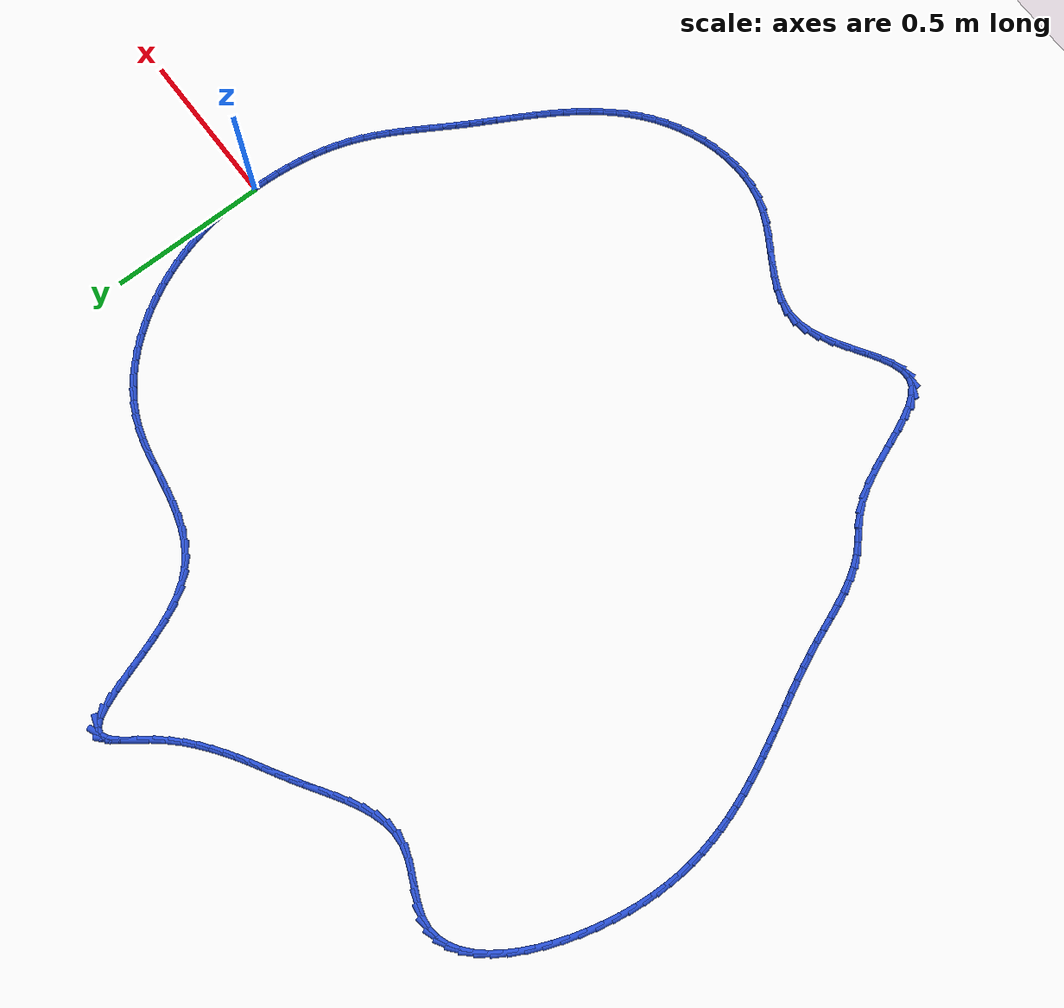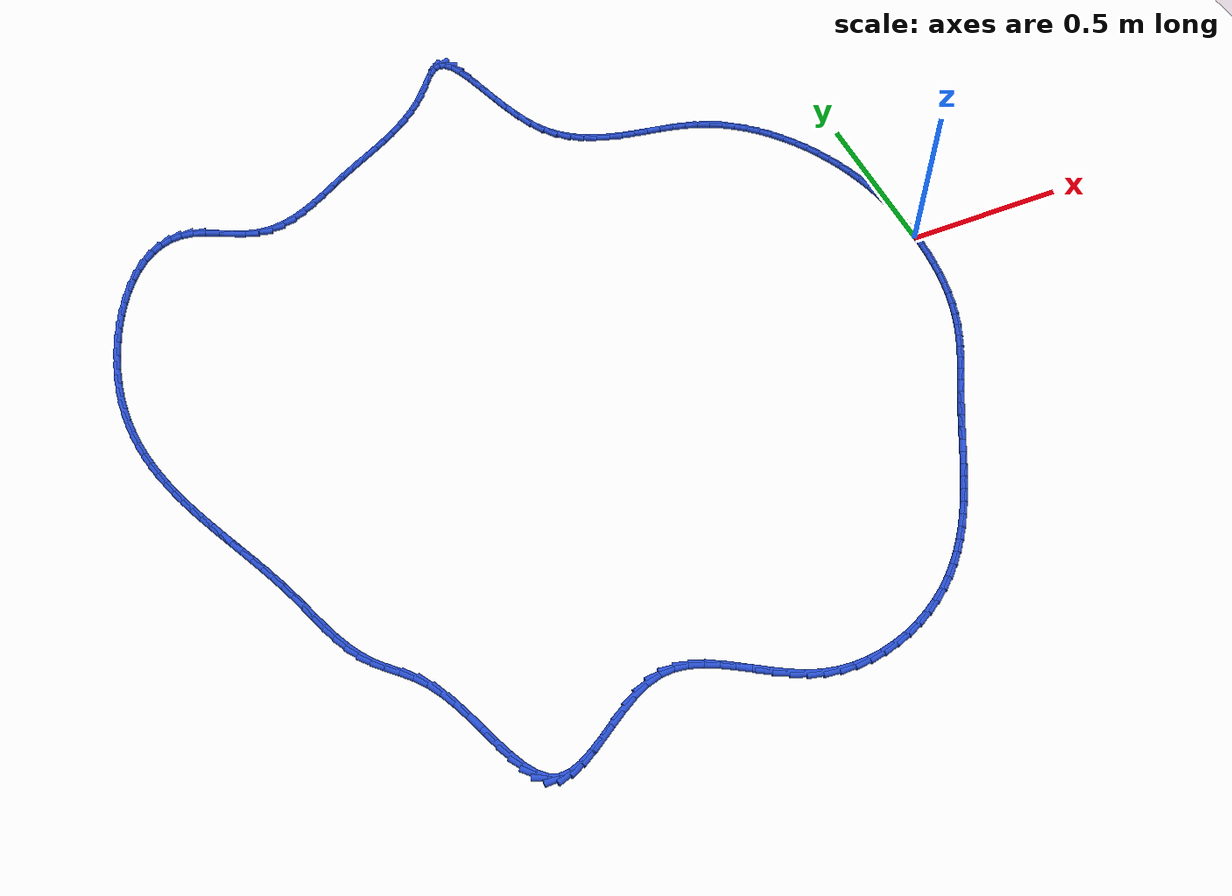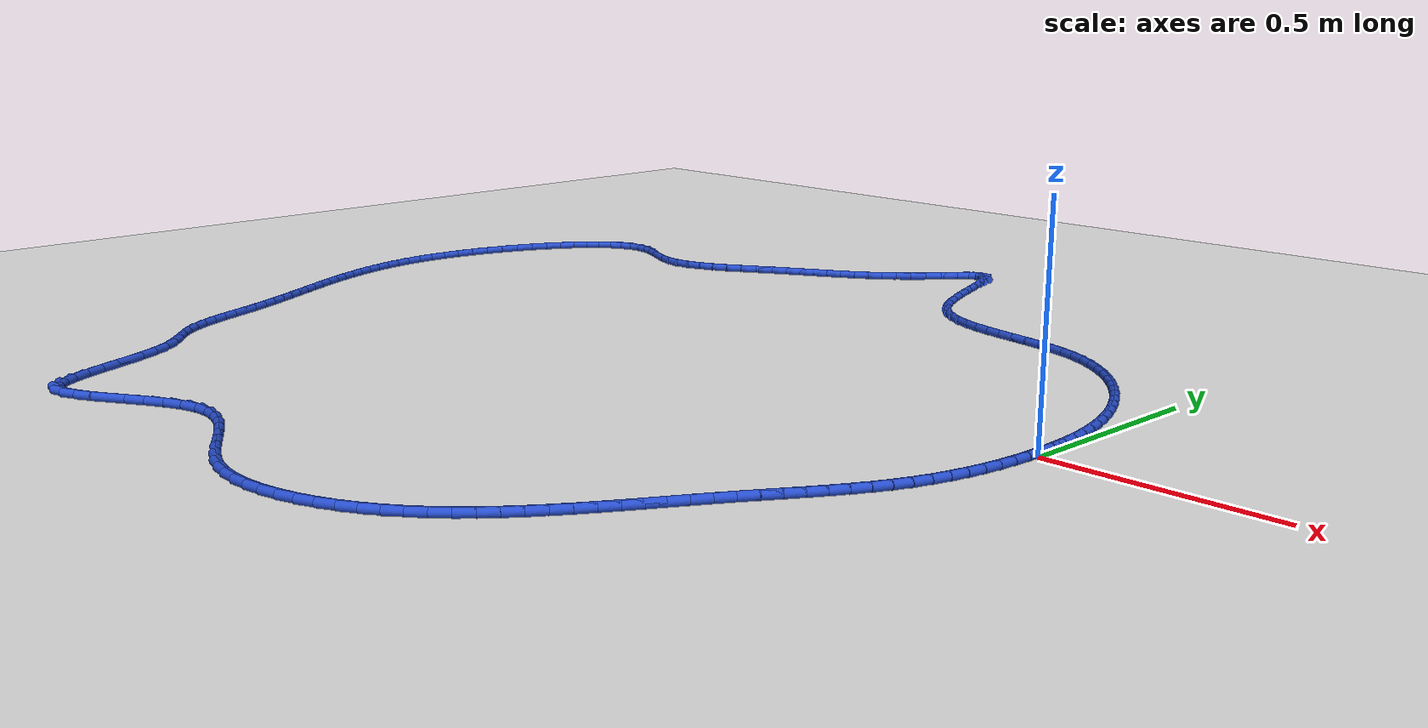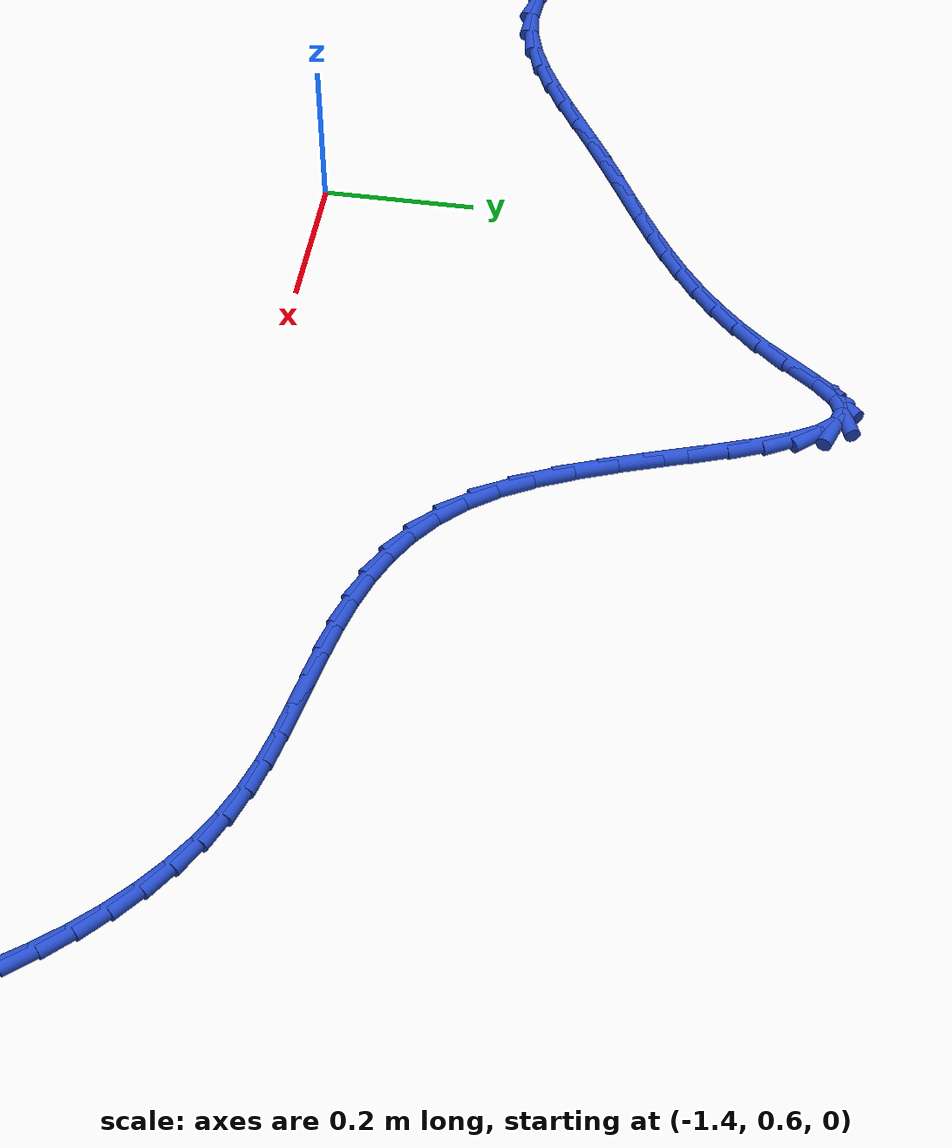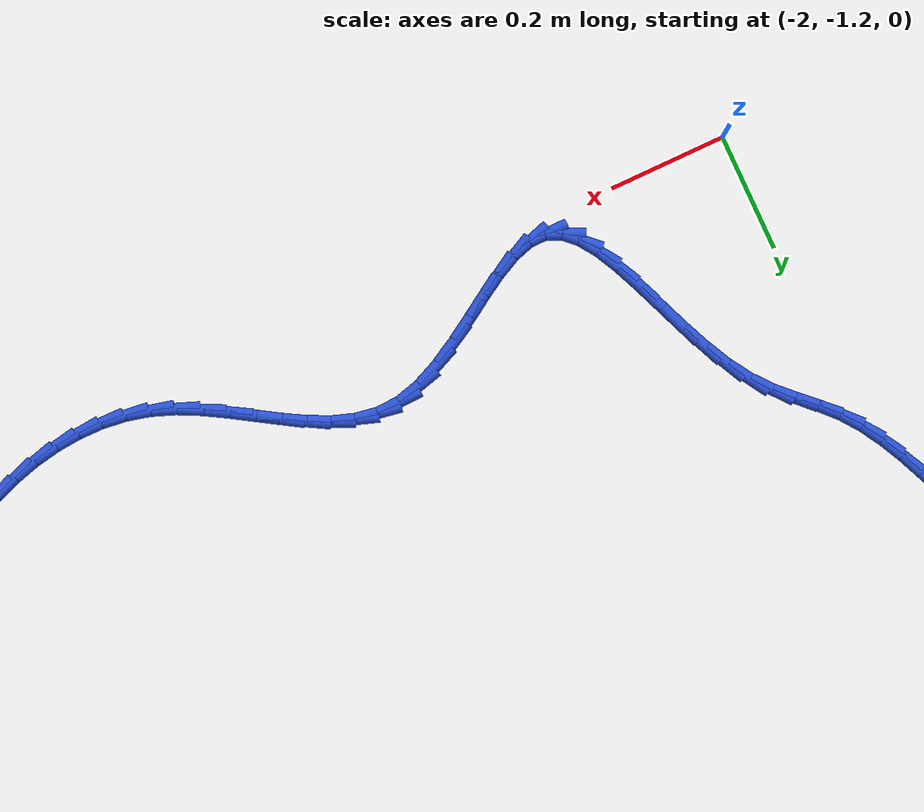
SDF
<sdf version="1.6">
 <world name="default">
  <light name="sun" type="directional">
   <pose>0 0 10 0 -0 0</pose>
   <diffuse>0.8 0.8 0.8 1</diffuse>
   <specular>0.2 0.2 0.2 1</specular>
   <attenuation>
    <range>1000</range>
    <constant>0.9</constant>
    <linear>0.01</linear>
    <quadratic>0.001</quadratic>
   </attenuation>
   <direction>-0.5 0.1 -0.9</direction>
  </light>
  <model name="ground_plane">
   <static>1</static>
   <link name="link">
    <collision name="collision">
     <geometry><plane><normal>0 0 1</normal><size>100 100</size></plane></geometry>
     <surface><friction><ode><mu>100</mu><mu2>50</mu2></ode></friction></surface>
    </collision>
    <visual name="visual">
     <cast_shadows>0</cast_shadows>
     <geometry><plane><normal>0 0 1</normal><size>100 100</size></plane></geometry>
     <material>
      <script><uri>file://media/materials/scripts/gazebo.material</uri><name>Gazebo/WhiteGlow</name></script>
     </material>
    </visual>
   </link>
  </model>
  <gravity>0 0 -9.8</gravity>
  <magnetic_field>6e-06 2.3e-05 -4.2e-05</magnetic_field>
  <atmosphere type="adiabatic"/>
  <physics name="default_physics" default="0" type="ode">
   <max_step_size>0.001</max_step_size>
   <real_time_factor>1</real_time_factor>
   <real_time_update_rate>1000</real_time_update_rate>
  </physics>
  <scene><ambient>0.4 0.4 0.4 1</ambient><background>0.7 0.7 0.7 1</background><shadows>1</shadows></scene>
  <spherical_coordinates>
   <surface_model>EARTH_WGS84</surface_model>
   <latitude_deg>0</latitude_deg>
   <longitude_deg>0</longitude_deg>
   <elevation>0</elevation>
   <heading_deg>0</heading_deg>
  </spherical_coordinates>
  <model name="line">
   <link name="link_0">
    <pose>2.168404344971009e-17 1.3877787807814457e-17 0.01 0 1.57 -1.5551212567801216</pose>
    <collision name="collision">
     <geometry><cylinder><radius>0.01</radius><length>0.08</length></cylinder></geometry>
    </collision>
    <visual name="visual">
     <material>
      <script><name>Gazebo/Blue</name><uri>file://media/materials/scripts/gazebo.material</uri></script>
     </material>
     <geometry><cylinder><radius>0.01</radius><length>0.08</length></cylinder></geometry>
    </visual>
   </link>
   <link name="link_1">
    <pose>-0.0006400076228072262 0.04082630591460163 0.01 0 1.57 -1.5184108999417012</pose>
    <collision name="collision">
     <geometry><cylinder><radius>0.01</radius><length>0.08</length></cylinder></geometry>
    </collision>
    <visual name="visual">
     <material>
      <script><name>Gazebo/Blue</name><uri>file://media/materials/scripts/gazebo.material</uri></script>
     </material>
     <geometry><cylinder><radius>0.01</radius><length>0.08</length></cylinder></geometry>
    </visual>
   </link>
   <link name="link_2">
    <pose>-0.0027711181989995273 0.08147044925881956 0.01 0 1.57 -1.4789455290635551</pose>
    <collision name="collision">
     <geometry><cylinder><radius>0.01</radius><length>0.08</length></cylinder></geometry>
    </collision>
    <visual name="visual">
     <material>
      <script><name>Gazebo/Blue</name><uri>file://media/materials/scripts/gazebo.material</uri></script>
     </material>
     <geometry><cylinder><radius>0.01</radius><length>0.08</length></cylinder></geometry>
    </visual>
   </link>
   <link name="link_3">
    <pose>-0.006496500507876481 0.12191538846278568 0.01 0 1.57 -1.4368041478772031</pose>
    <collision name="collision">
     <geometry><cylinder><radius>0.01</radius><length>0.08</length></cylinder></geometry>
    </collision>
    <visual name="visual">
     <material>
      <script><name>Gazebo/Blue</name><uri>file://media/materials/scripts/gazebo.material</uri></script>
     </material>
     <geometry><cylinder><radius>0.01</radius><length>0.08</length></cylinder></geometry>
    </visual>
   </link>
   <link name="link_4">
    <pose>-0.011919323328737685 0.1621440819566316 0.01 0 1.57 -1.3921159415532443</pose>
    <collision name="collision">
     <geometry><cylinder><radius>0.01</radius><length>0.08</length></cylinder></geometry>
    </collision>
    <visual name="visual">
     <material>
      <script><name>Gazebo/Blue</name><uri>file://media/materials/scripts/gazebo.material</uri></script>
     </material>
     <geometry><cylinder><radius>0.01</radius><length>0.08</length></cylinder></geometry>
    </visual>
   </link>
   <link name="link_5">
    <pose>-0.019142755440882744 0.2021394881704891 0.01 0 1.57 -1.3450662787510348</pose>
    <collision name="collision">
     <geometry><cylinder><radius>0.01</radius><length>0.08</length></cylinder></geometry>
    </collision>
    <visual name="visual">
     <material>
      <script><name>Gazebo/Blue</name><uri>file://media/materials/scripts/gazebo.material</uri></script>
     </material>
     <geometry><cylinder><radius>0.01</radius><length>0.08</length></cylinder></geometry>
    </visual>
   </link>
   <link name="link_6">
    <pose>-0.028269965623611257 0.24188456553449006 0.01 0 1.57 -1.2959001138740873</pose>
    <collision name="collision">
     <geometry><cylinder><radius>0.01</radius><length>0.08</length></cylinder></geometry>
    </collision>
    <visual name="visual">
     <material>
      <script><name>Gazebo/Blue</name><uri>file://media/materials/scripts/gazebo.material</uri></script>
     </material>
     <geometry><cylinder><radius>0.01</radius><length>0.08</length></cylinder></geometry>
    </visual>
   </link>
   <link name="link_7">
    <pose>-0.0394041226562228 0.281362272478766 0.01 0 1.57 -1.244921763635171</pose>
    <collision name="collision">
     <geometry><cylinder><radius>0.01</radius><length>0.08</length></cylinder></geometry>
    </collision>
    <visual name="visual">
     <material>
      <script><name>Gazebo/Blue</name><uri>file://media/materials/scripts/gazebo.material</uri></script>
     </material>
     <geometry><cylinder><radius>0.01</radius><length>0.08</length></cylinder></geometry>
    </visual>
   </link>
   <link name="link_8">
    <pose>-0.052648395318017016 0.32055556743344893 0.01 0 1.57 -1.1926634956411664</pose>
    <collision name="collision">
     <geometry><cylinder><radius>0.01</radius><length>0.08</length></cylinder></geometry>
    </collision>
    <visual name="visual">
     <material>
      <script><name>Gazebo/Blue</name><uri>file://media/materials/scripts/gazebo.material</uri></script>
     </material>
     <geometry><cylinder><radius>0.01</radius><length>0.08</length></cylinder></geometry>
    </visual>
   </link>
   <link name="link_9">
    <pose>-0.06808680993118768 0.3594188577691552 0.01 0 1.57 -1.140107194867661</pose>
    <collision name="collision">
     <geometry><cylinder><radius>0.01</radius><length>0.08</length></cylinder></geometry>
    </collision>
    <visual name="visual">
     <material>
      <script><name>Gazebo/Blue</name><uri>file://media/materials/scripts/gazebo.material</uri></script>
     </material>
     <geometry><cylinder><radius>0.01</radius><length>0.08</length></cylinder></geometry>
    </visual>
   </link>
   <link name="link_10">
    <pose>-0.08569788404906521 0.3977491840606631 0.01 0 1.57 -1.0869871817703625</pose>
    <collision name="collision">
     <geometry><cylinder><radius>0.01</radius><length>0.08</length></cylinder></geometry>
    </collision>
    <visual name="visual">
     <material>
      <script><name>Gazebo/Blue</name><uri>file://media/materials/scripts/gazebo.material</uri></script>
     </material>
     <geometry><cylinder><radius>0.01</radius><length>0.08</length></cylinder></geometry>
    </visual>
   </link>
   <link name="link_11">
    <pose>-0.10542398008695125 0.4352896613343259 0.01 0 1.57 -1.0326520526870329</pose>
    <collision name="collision">
     <geometry><cylinder><radius>0.01</radius><length>0.08</length></cylinder></geometry>
    </collision>
    <visual name="visual">
     <material>
      <script><name>Gazebo/Blue</name><uri>file://media/materials/scripts/gazebo.material</uri></script>
     </material>
     <geometry><cylinder><radius>0.01</radius><length>0.08</length></cylinder></geometry>
    </visual>
   </link>
   <link name="link_12">
    <pose>-0.1272074283758707 0.47178335676265554 0.01 0 1.57 -0.9764632923842738</pose>
    <collision name="collision">
     <geometry><cylinder><radius>0.01</radius><length>0.08</length></cylinder></geometry>
    </collision>
    <visual name="visual">
     <material>
      <script><name>Gazebo/Blue</name><uri>file://media/materials/scripts/gazebo.material</uri></script>
     </material>
     <geometry><cylinder><radius>0.01</radius><length>0.08</length></cylinder></geometry>
    </visual>
   </link>
   <link name="link_13">
    <pose>-0.15099055924684845 0.506973337518164 0.01 0 1.57 -0.9177884465022511</pose>
    <collision name="collision">
     <geometry><cylinder><radius>0.01</radius><length>0.08</length></cylinder></geometry>
    </collision>
    <visual name="visual">
     <material>
      <script><name>Gazebo/Blue</name><uri>file://media/materials/scripts/gazebo.material</uri></script>
     </material>
     <geometry><cylinder><radius>0.01</radius><length>0.08</length></cylinder></geometry>
    </visual>
   </link>
   <link name="link_14">
    <pose>-0.1767157030309095 0.5406026707733635 0.01 0 1.57 -0.8560005480095294</pose>
    <collision name="collision">
     <geometry><cylinder><radius>0.01</radius><length>0.08</length></cylinder></geometry>
    </collision>
    <visual name="visual">
     <material>
      <script><name>Gazebo/Blue</name><uri>file://media/materials/scripts/gazebo.material</uri></script>
     </material>
     <geometry><cylinder><radius>0.01</radius><length>0.08</length></cylinder></geometry>
    </visual>
   </link>
   <link name="link_15">
    <pose>-0.20432519005907876 0.5724144237007665 0.01 0 1.57 -0.7904862024280711</pose>
    <collision name="collision">
     <geometry><cylinder><radius>0.01</radius><length>0.08</length></cylinder></geometry>
    </collision>
    <visual name="visual">
     <material>
      <script><name>Gazebo/Blue</name><uri>file://media/materials/scripts/gazebo.material</uri></script>
     </material>
     <geometry><cylinder><radius>0.01</radius><length>0.08</length></cylinder></geometry>
    </visual>
   </link>
   <link name="link_16">
    <pose>-0.2337613506623813 0.602151663472885 0.01 0 1.57 -0.7206651776646534</pose>
    <collision name="collision">
     <geometry><cylinder><radius>0.01</radius><length>0.08</length></cylinder></geometry>
    </collision>
    <visual name="visual">
     <material>
      <script><name>Gazebo/Blue</name><uri>file://media/materials/scripts/gazebo.material</uri></script>
     </material>
     <geometry><cylinder><radius>0.01</radius><length>0.08</length></cylinder></geometry>
    </visual>
   </link>
   <link name="link_17">
    <pose>-0.2649665151718419 0.6295574572622309 0.01 0 1.57 -0.6460247213195862</pose>
    <collision name="collision">
     <geometry><cylinder><radius>0.01</radius><length>0.08</length></cylinder></geometry>
    </collision>
    <visual name="visual">
     <material>
      <script><name>Gazebo/Blue</name><uri>file://media/materials/scripts/gazebo.material</uri></script>
     </material>
     <geometry><cylinder><radius>0.01</radius><length>0.08</length></cylinder></geometry>
    </visual>
   </link>
   <link name="link_18">
    <pose>-0.2978830139184856 0.654374872241317 0.01 0 1.57 -0.566171233026452</pose>
    <collision name="collision">
     <geometry><cylinder><radius>0.01</radius><length>0.08</length></cylinder></geometry>
    </collision>
    <visual name="visual">
     <material>
      <script><name>Gazebo/Blue</name><uri>file://media/materials/scripts/gazebo.material</uri></script>
     </material>
     <geometry><cylinder><radius>0.01</radius><length>0.08</length></cylinder></geometry>
    </visual>
   </link>
   <link name="link_19">
    <pose>-0.33245317723333717 0.6763469755826547 0.01 0 1.57 -0.48089942804368385</pose>
    <collision name="collision">
     <geometry><cylinder><radius>0.01</radius><length>0.08</length></cylinder></geometry>
    </collision>
    <visual name="visual">
     <material>
      <script><name>Gazebo/Blue</name><uri>file://media/materials/scripts/gazebo.material</uri></script>
     </material>
     <geometry><cylinder><radius>0.01</radius><length>0.08</length></cylinder></geometry>
    </visual>
   </link>
   <link name="link_20">
    <pose>-0.36861933544742187 0.6952168344587567 0.01 0 1.57 -0.3903455812087128</pose>
    <collision name="collision">
     <geometry><cylinder><radius>0.01</radius><length>0.08</length></cylinder></geometry>
    </collision>
    <visual name="visual">
     <material>
      <script><name>Gazebo/Blue</name><uri>file://media/materials/scripts/gazebo.material</uri></script>
     </material>
     <geometry><cylinder><radius>0.01</radius><length>0.08</length></cylinder></geometry>
    </visual>
   </link>
   <link name="link_21">
    <pose>-0.4063230328004683 0.7107303580053506 0.01 0 1.57 -0.303716786756883</pose>
    <collision name="collision">
     <geometry><cylinder><radius>0.01</radius><length>0.08</length></cylinder></geometry>
    </collision>
    <visual name="visual">
     <material>
      <script><name>Gazebo/Blue</name><uri>file://media/materials/scripts/gazebo.material</uri></script>
     </material>
     <geometry><cylinder><radius>0.01</radius><length>0.08</length></cylinder></geometry>
    </visual>
   </link>
   <link name="link_22">
    <pose>-0.4454097744053602 0.7229806665117052 0.01 0 1.57 -0.2385015430849483</pose>
    <collision name="collision">
     <geometry><cylinder><radius>0.01</radius><length>0.08</length></cylinder></geometry>
    </collision>
    <visual name="visual">
     <material>
      <script><name>Gazebo/Blue</name><uri>file://media/materials/scripts/gazebo.material</uri></script>
     </material>
     <geometry><cylinder><radius>0.01</radius><length>0.08</length></cylinder></geometry>
    </visual>
   </link>
   <link name="link_23">
    <pose>-0.48553804509367693 0.7327370164393013 0.01 0 1.57 -0.19617558059812404</pose>
    <collision name="collision">
     <geometry><cylinder><radius>0.01</radius><length>0.08</length></cylinder></geometry>
    </collision>
    <visual name="visual">
     <material>
      <script><name>Gazebo/Blue</name><uri>file://media/materials/scripts/gazebo.material</uri></script>
     </material>
     <geometry><cylinder><radius>0.01</radius><length>0.08</length></cylinder></geometry>
    </visual>
   </link>
   <link name="link_24">
    <pose>-0.5263447725933722 0.7408465998479788 0.01 0 1.57 -0.17592574702107977</pose>
    <collision name="collision">
     <geometry><cylinder><radius>0.01</radius><length>0.08</length></cylinder></geometry>
    </collision>
    <visual name="visual">
     <material>
      <script><name>Gazebo/Blue</name><uri>file://media/materials/scripts/gazebo.material</uri></script>
     </material>
     <geometry><cylinder><radius>0.01</radius><length>0.08</length></cylinder></geometry>
    </visual>
   </link>
   <link name="link_25">
    <pose>-0.5674668846324007 0.7481566087975784 0.01 0 1.57 -0.17724928655361932</pose>
    <collision name="collision">
     <geometry><cylinder><radius>0.01</radius><length>0.08</length></cylinder></geometry>
    </collision>
    <visual name="visual">
     <material>
      <script><name>Gazebo/Blue</name><uri>file://media/materials/scripts/gazebo.material</uri></script>
     </material>
     <geometry><cylinder><radius>0.01</radius><length>0.08</length></cylinder></geometry>
    </visual>
   </link>
   <link name="link_26">
    <pose>-0.6085413089387165 0.7555142353479405 0.01 0 1.57 -0.20022447232874</pose>
    <collision name="collision">
     <geometry><cylinder><radius>0.01</radius><length>0.08</length></cylinder></geometry>
    </collision>
    <visual name="visual">
     <material>
      <script><name>Gazebo/Blue</name><uri>file://media/materials/scripts/gazebo.material</uri></script>
     </material>
     <geometry><cylinder><radius>0.01</radius><length>0.08</length></cylinder></geometry>
    </visual>
   </link>
   <link name="link_27">
    <pose>-0.6492049732402734 0.763766671558905 0.01 0 1.57 -0.24549719889906232</pose>
    <collision name="collision">
     <geometry><cylinder><radius>0.01</radius><length>0.08</length></cylinder></geometry>
    </collision>
    <visual name="visual">
     <material>
      <script><name>Gazebo/Blue</name><uri>file://media/materials/scripts/gazebo.material</uri></script>
     </material>
     <geometry><cylinder><radius>0.01</radius><length>0.08</length></cylinder></geometry>
    </visual>
   </link>
   <link name="link_28">
    <pose>-0.6890948052650263 0.7737611094903126 0.01 0 1.57 -0.31397351804022045</pose>
    <collision name="collision">
     <geometry><cylinder><radius>0.01</radius><length>0.08</length></cylinder></geometry>
    </collision>
    <visual name="visual">
     <material>
      <script><name>Gazebo/Blue</name><uri>file://media/materials/scripts/gazebo.material</uri></script>
     </material>
     <geometry><cylinder><radius>0.01</radius><length>0.08</length></cylinder></geometry>
    </visual>
   </link>
   <link name="link_29">
    <pose>-0.7278477327409286 0.786344741202003 0.01 0 1.57 -0.40612634844174816</pose>
    <collision name="collision">
     <geometry><cylinder><radius>0.01</radius><length>0.08</length></cylinder></geometry>
    </collision>
    <visual name="visual">
     <material>
      <script><name>Gazebo/Blue</name><uri>file://media/materials/scripts/gazebo.material</uri></script>
     </material>
     <geometry><cylinder><radius>0.01</radius><length>0.08</length></cylinder></geometry>
    </visual>
   </link>
   <link name="link_30">
    <pose>-0.7651006833959353 0.8023647587538172 0.01 0 1.57 -0.520865439983375</pose>
    <collision name="collision">
     <geometry><cylinder><radius>0.01</radius><length>0.08</length></cylinder></geometry>
    </collision>
    <visual name="visual">
     <material>
      <script><name>Gazebo/Blue</name><uri>file://media/materials/scripts/gazebo.material</uri></script>
     </material>
     <geometry><cylinder><radius>0.01</radius><length>0.08</length></cylinder></geometry>
    </visual>
   </link>
   <link name="link_31">
    <pose>-0.8004905849580001 0.8226683542055954 0.01 0 1.57 -0.6542498344690967</pose>
    <collision name="collision">
     <geometry><cylinder><radius>0.01</radius><length>0.08</length></cylinder></geometry>
    </collision>
    <visual name="visual">
     <material>
      <script><name>Gazebo/Blue</name><uri>file://media/materials/scripts/gazebo.material</uri></script>
     </material>
     <geometry><cylinder><radius>0.01</radius><length>0.08</length></cylinder></geometry>
    </visual>
   </link>
   <link name="link_32">
    <pose>-0.8336543651550772 0.8481027196171774 0.01 0 1.57 -0.79891214269424</pose>
    <collision name="collision">
     <geometry><cylinder><radius>0.01</radius><length>0.08</length></cylinder></geometry>
    </collision>
    <visual name="visual">
     <material>
      <script><name>Gazebo/Blue</name><uri>file://media/materials/scripts/gazebo.material</uri></script>
     </material>
     <geometry><cylinder><radius>0.01</radius><length>0.08</length></cylinder></geometry>
    </visual>
   </link>
   <link name="link_33">
    <pose>-0.8642289517151212 0.8795150470484041 0.01 0 1.57 -0.9451556518203059</pose>
    <collision name="collision">
     <geometry><cylinder><radius>0.01</radius><length>0.08</length></cylinder></geometry>
    </collision>
    <visual name="visual">
     <material>
      <script><name>Gazebo/Blue</name><uri>file://media/materials/scripts/gazebo.material</uri></script>
     </material>
     <geometry><cylinder><radius>0.01</radius><length>0.08</length></cylinder></geometry>
    </visual>
   </link>
   <link name="link_34">
    <pose>-0.8918520325826715 0.9177498512966816 0.01 0 1.57 -1.0721236686585107</pose>
    <collision name="collision">
     <geometry><cylinder><radius>0.01</radius><length>0.08</length></cylinder></geometry>
    </collision>
    <visual name="visual">
     <material>
      <script><name>Gazebo/Blue</name><uri>file://media/materials/scripts/gazebo.material</uri></script>
     </material>
     <geometry><cylinder><radius>0.01</radius><length>0.08</length></cylinder></geometry>
    </visual>
   </link>
   <link name="link_35">
    <pose>-0.9163970678294107 0.9628213260764397 0.01 0 1.57 -1.1572292377738818</pose>
    <collision name="collision">
     <geometry><cylinder><radius>0.01</radius><length>0.08</length></cylinder></geometry>
    </collision>
    <visual name="visual">
     <material>
      <script><name>Gazebo/Blue</name><uri>file://media/materials/scripts/gazebo.material</uri></script>
     </material>
     <geometry><cylinder><radius>0.01</radius><length>0.08</length></cylinder></geometry>
    </visual>
   </link>
   <link name="link_36">
    <pose>-0.9383060116720581 1.0127415935260686 0.01 0 1.57 -1.210077566266756</pose>
    <collision name="collision">
     <geometry><cylinder><radius>0.01</radius><length>0.08</length></cylinder></geometry>
    </collision>
    <visual name="visual">
     <material>
      <script><name>Gazebo/Blue</name><uri>file://media/materials/scripts/gazebo.material</uri></script>
     </material>
     <geometry><cylinder><radius>0.01</radius><length>0.08</length></cylinder></geometry>
    </visual>
   </link>
   <link name="link_37">
    <pose>-0.958104780886987 1.0652270839890587 0.01 0 1.57 -1.2384160266182476</pose>
    <collision name="collision">
     <geometry><cylinder><radius>0.01</radius><length>0.08</length></cylinder></geometry>
    </collision>
    <visual name="visual">
     <material>
      <script><name>Gazebo/Blue</name><uri>file://media/materials/scripts/gazebo.material</uri></script>
     </material>
     <geometry><cylinder><radius>0.01</radius><length>0.08</length></cylinder></geometry>
    </visual>
   </link>
   <link name="link_38">
    <pose>-0.9763192922505707 1.117994227808902 0.01 0 1.57 -1.2448954530257224</pose>
    <collision name="collision">
     <geometry><cylinder><radius>0.01</radius><length>0.08</length></cylinder></geometry>
    </collision>
    <visual name="visual">
     <material>
      <script><name>Gazebo/Blue</name><uri>file://media/materials/scripts/gazebo.material</uri></script>
     </material>
     <geometry><cylinder><radius>0.01</radius><length>0.08</length></cylinder></geometry>
    </visual>
   </link>
   <link name="link_39">
    <pose>-0.9934754625391832 1.1687594553290894 0.01 0 1.57 -1.2273176029879977</pose>
    <collision name="collision">
     <geometry><cylinder><radius>0.01</radius><length>0.08</length></cylinder></geometry>
    </collision>
    <visual name="visual">
     <material>
      <script><name>Gazebo/Blue</name><uri>file://media/materials/scripts/gazebo.material</uri></script>
     </material>
     <geometry><cylinder><radius>0.01</radius><length>0.08</length></cylinder></geometry>
    </visual>
   </link>
   <link name="link_40">
    <pose>-1.010099208529197 1.2152391968931118 0.01 0 1.57 -1.1762659978039807</pose>
    <collision name="collision">
     <geometry><cylinder><radius>0.01</radius><length>0.08</length></cylinder></geometry>
    </collision>
    <visual name="visual">
     <material>
      <script><name>Gazebo/Blue</name><uri>file://media/materials/scripts/gazebo.material</uri></script>
     </material>
     <geometry><cylinder><radius>0.01</radius><length>0.08</length></cylinder></geometry>
    </visual>
   </link>
   <link name="link_41">
    <pose>-1.0267164469969865 1.2551498828444614 0.01 0 1.57 -1.066601585094985</pose>
    <collision name="collision">
     <geometry><cylinder><radius>0.01</radius><length>0.08</length></cylinder></geometry>
    </collision>
    <visual name="visual">
     <material>
      <script><name>Gazebo/Blue</name><uri>file://media/materials/scripts/gazebo.material</uri></script>
     </material>
     <geometry><cylinder><radius>0.01</radius><length>0.08</length></cylinder></geometry>
    </visual>
   </link>
   <link name="link_42">
    <pose>-1.0438530947189246 1.2862079435266291 0.01 0 1.57 -0.8310283232203267</pose>
    <collision name="collision">
     <geometry><cylinder><radius>0.01</radius><length>0.08</length></cylinder></geometry>
    </collision>
    <visual name="visual">
     <material>
      <script><name>Gazebo/Blue</name><uri>file://media/materials/scripts/gazebo.material</uri></script>
     </material>
     <geometry><cylinder><radius>0.01</radius><length>0.08</length></cylinder></geometry>
    </visual>
   </link>
   <link name="link_43">
    <pose>-1.062035068471385 1.3061298092831062 0.01 0 1.57 -0.31799591171986696</pose>
    <collision name="collision">
     <geometry><cylinder><radius>0.01</radius><length>0.08</length></cylinder></geometry>
    </collision>
    <visual name="visual">
     <material>
      <script><name>Gazebo/Blue</name><uri>file://media/materials/scripts/gazebo.material</uri></script>
     </material>
     <geometry><cylinder><radius>0.01</radius><length>0.08</length></cylinder></geometry>
    </visual>
   </link>
   <link name="link_44">
    <pose>-1.0817882850307412 1.3126319104573838 0.01 0 1.57 0.39846431778704694</pose>
    <collision name="collision">
     <geometry><cylinder><radius>0.01</radius><length>0.08</length></cylinder></geometry>
    </collision>
    <visual name="visual">
     <material>
      <script><name>Gazebo/Blue</name><uri>file://media/materials/scripts/gazebo.material</uri></script>
     </material>
     <geometry><cylinder><radius>0.01</radius><length>0.08</length></cylinder></geometry>
    </visual>
   </link>
   <link name="link_45">
    <pose>-1.1036383635805154 1.303433372615789 0.01 0 1.57 0.8002993296854736</pose>
    <collision name="collision">
     <geometry><cylinder><radius>0.01</radius><length>0.08</length></cylinder></geometry>
    </collision>
    <visual name="visual">
     <material>
      <script><name>Gazebo/Blue</name><uri>file://media/materials/scripts/gazebo.material</uri></script>
     </material>
     <geometry><cylinder><radius>0.01</radius><length>0.08</length></cylinder></geometry>
    </visual>
   </link>
   <link name="link_46">
    <pose>-1.1278658517911588 1.2784728717458058 0.01 0 1.57 0.9220185095705806</pose>
    <collision name="collision">
     <geometry><cylinder><radius>0.01</radius><length>0.08</length></cylinder></geometry>
    </collision>
    <visual name="visual">
     <material>
      <script><name>Gazebo/Blue</name><uri>file://media/materials/scripts/gazebo.material</uri></script>
     </material>
     <geometry><cylinder><radius>0.01</radius><length>0.08</length></cylinder></geometry>
    </visual>
   </link>
   <link name="link_47">
    <pose>-1.1540627636269758 1.2439249586549355 0.01 0 1.57 0.9276211665145389</pose>
    <collision name="collision">
     <geometry><cylinder><radius>0.01</radius><length>0.08</length></cylinder></geometry>
    </collision>
    <visual name="visual">
     <material>
      <script><name>Gazebo/Blue</name><uri>file://media/materials/scripts/gazebo.material</uri></script>
     </material>
     <geometry><cylinder><radius>0.01</radius><length>0.08</length></cylinder></geometry>
    </visual>
   </link>
   <link name="link_48">
    <pose>-1.1817012509308837 1.207048607135749 0.01 0 1.57 0.8671612460572974</pose>
    <collision name="collision">
     <geometry><cylinder><radius>0.01</radius><length>0.08</length></cylinder></geometry>
    </collision>
    <visual name="visual">
     <material>
      <script><name>Gazebo/Blue</name><uri>file://media/materials/scripts/gazebo.material</uri></script>
     </material>
     <geometry><cylinder><radius>0.01</radius><length>0.08</length></cylinder></geometry>
    </visual>
   </link>
   <link name="link_49">
    <pose>-1.2103682517319463 1.173263957631426 0.01 0 1.57 0.7976299146507713</pose>
    <collision name="collision">
     <geometry><cylinder><radius>0.01</radius><length>0.08</length></cylinder></geometry>
    </collision>
    <visual name="visual">
     <material>
      <script><name>Gazebo/Blue</name><uri>file://media/materials/scripts/gazebo.material</uri></script>
     </material>
     <geometry><cylinder><radius>0.01</radius><length>0.08</length></cylinder></geometry>
    </visual>
   </link>
   <link name="link_50">
    <pose>-1.2399664722741899 1.1429326575396117 0.01 0 1.57 0.7317486666701256</pose>
    <collision name="collision">
     <geometry><cylinder><radius>0.01</radius><length>0.08</length></cylinder></geometry>
    </collision>
    <visual name="visual">
     <material>
      <script><name>Gazebo/Blue</name><uri>file://media/materials/scripts/gazebo.material</uri></script>
     </material>
     <geometry><cylinder><radius>0.01</radius><length>0.08</length></cylinder></geometry>
    </visual>
   </link>
   <link name="link_51">
    <pose>-1.270452445449271 1.1155540707544225 0.01 0 1.57 0.6720552955293879</pose>
    <collision name="collision">
     <geometry><cylinder><radius>0.01</radius><length>0.08</length></cylinder></geometry>
    </collision>
    <visual name="visual">
     <material>
      <script><name>Gazebo/Blue</name><uri>file://media/materials/scripts/gazebo.material</uri></script>
     </material>
     <geometry><cylinder><radius>0.01</radius><length>0.08</length></cylinder></geometry>
    </visual>
   </link>
   <link name="link_52">
    <pose>-1.3017827041488452 1.0906275611699736 0.01 0 1.57 0.6207500669049182</pose>
    <collision name="collision">
     <geometry><cylinder><radius>0.01</radius><length>0.08</length></cylinder></geometry>
    </collision>
    <visual name="visual">
     <material>
      <script><name>Gazebo/Blue</name><uri>file://media/materials/scripts/gazebo.material</uri></script>
     </material>
     <geometry><cylinder><radius>0.01</radius><length>0.08</length></cylinder></geometry>
    </visual>
   </link>
   <link name="link_53">
    <pose>-1.3339137812645683 1.0676524926803814 0.01 0 1.57 0.5795063437029108</pose>
    <collision name="collision">
     <geometry><cylinder><radius>0.01</radius><length>0.08</length></cylinder></geometry>
    </collision>
    <visual name="visual">
     <material>
      <script><name>Gazebo/Blue</name><uri>file://media/materials/scripts/gazebo.material</uri></script>
     </material>
     <geometry><cylinder><radius>0.01</radius><length>0.08</length></cylinder></geometry>
    </visual>
   </link>
   <link name="link_54">
    <pose>-1.3668022096880974 1.0461282291797604 0.01 0 1.57 0.5494015451554398</pose>
    <collision name="collision">
     <geometry><cylinder><radius>0.01</radius><length>0.08</length></cylinder></geometry>
    </collision>
    <visual name="visual">
     <material>
      <script><name>Gazebo/Blue</name><uri>file://media/materials/scripts/gazebo.material</uri></script>
     </material>
     <geometry><cylinder><radius>0.01</radius><length>0.08</length></cylinder></geometry>
    </visual>
   </link>
   <link name="link_55">
    <pose>-1.4004045223110875 1.0255541345622268 0.01 0 1.57 0.5309462133035222</pose>
    <collision name="collision">
     <geometry><cylinder><radius>0.01</radius><length>0.08</length></cylinder></geometry>
    </collision>
    <visual name="visual">
     <material>
      <script><name>Gazebo/Blue</name><uri>file://media/materials/scripts/gazebo.material</uri></script>
     </material>
     <geometry><cylinder><radius>0.01</radius><length>0.08</length></cylinder></geometry>
    </visual>
   </link>
   <link name="link_56">
    <pose>-1.4346772520251951 1.0054295727218967 0.01 0 1.57 0.5241643345688503</pose>
    <collision name="collision">
     <geometry><cylinder><radius>0.01</radius><length>0.08</length></cylinder></geometry>
    </collision>
    <visual name="visual">
     <material>
      <script><name>Gazebo/Blue</name><uri>file://media/materials/scripts/gazebo.material</uri></script>
     </material>
     <geometry><cylinder><radius>0.01</radius><length>0.08</length></cylinder></geometry>
    </visual>
   </link>
   <link name="link_57">
    <pose>-1.4695769317220766 0.985253907552885 0.01 0 1.57 0.5286817761652555</pose>
    <collision name="collision">
     <geometry><cylinder><radius>0.01</radius><length>0.08</length></cylinder></geometry>
    </collision>
    <visual name="visual">
     <material>
      <script><name>Gazebo/Blue</name><uri>file://media/materials/scripts/gazebo.material</uri></script>
     </material>
     <geometry><cylinder><radius>0.01</radius><length>0.08</length></cylinder></geometry>
    </visual>
   </link>
   <link name="link_58">
    <pose>-1.5050600942933878 0.964526502949308 0.01 0 1.57 0.5437983752880435</pose>
    <collision name="collision">
     <geometry><cylinder><radius>0.01</radius><length>0.08</length></cylinder></geometry>
    </collision>
    <visual name="visual">
     <material>
      <script><name>Gazebo/Blue</name><uri>file://media/materials/scripts/gazebo.material</uri></script>
     </material>
     <geometry><cylinder><radius>0.01</radius><length>0.08</length></cylinder></geometry>
    </visual>
   </link>
   <link name="link_59">
    <pose>-1.5410832726307842 0.9427467228052807 0.01 0 1.57 0.5640622509140586</pose>
    <collision name="collision">
     <geometry><cylinder><radius>0.01</radius><length>0.08</length></cylinder></geometry>
    </collision>
    <visual name="visual">
     <material>
      <script><name>Gazebo/Blue</name><uri>file://media/materials/scripts/gazebo.material</uri></script>
     </material>
     <geometry><cylinder><radius>0.01</radius><length>0.08</length></cylinder></geometry>
    </visual>
   </link>
   <link name="link_60">
    <pose>-1.5776025631585504 0.9196437797439346 0.01 0 1.57 0.5661444793515885</pose>
    <collision name="collision">
     <geometry><cylinder><radius>0.01</radius><length>0.08</length></cylinder></geometry>
    </collision>
    <visual name="visual">
     <material>
      <script><name>Gazebo/Blue</name><uri>file://media/materials/scripts/gazebo.material</uri></script>
     </material>
     <geometry><cylinder><radius>0.01</radius><length>0.08</length></cylinder></geometry>
    </visual>
   </link>
   <link name="link_61">
    <pose>-1.6145717809461695 0.8961482740165974 0.01 0 1.57 0.5432266460889836</pose>
    <collision name="collision">
     <geometry><cylinder><radius>0.01</radius><length>0.08</length></cylinder></geometry>
    </collision>
    <visual name="visual">
     <material>
      <script><name>Gazebo/Blue</name><uri>file://media/materials/scripts/gazebo.material</uri></script>
     </material>
     <geometry><cylinder><radius>0.01</radius><length>0.08</length></cylinder></geometry>
    </visual>
   </link>
   <link name="link_62">
    <pose>-1.651943998162261 0.8735820259990037 0.01 0 1.57 0.4939357228277672</pose>
    <collision name="collision">
     <geometry><cylinder><radius>0.01</radius><length>0.08</length></cylinder></geometry>
    </collision>
    <visual name="visual">
     <material>
      <script><name>Gazebo/Blue</name><uri>file://media/materials/scripts/gazebo.material</uri></script>
     </material>
     <geometry><cylinder><radius>0.01</radius><length>0.08</length></cylinder></geometry>
    </visual>
   </link>
   <link name="link_63">
    <pose>-1.6896722865719374 0.8532670685573894 0.01 0 1.57 0.41462061402821904</pose>
    <collision name="collision">
     <geometry><cylinder><radius>0.01</radius><length>0.08</length></cylinder></geometry>
    </collision>
    <visual name="visual">
     <material>
      <script><name>Gazebo/Blue</name><uri>file://media/materials/scripts/gazebo.material</uri></script>
     </material>
     <geometry><cylinder><radius>0.01</radius><length>0.08</length></cylinder></geometry>
    </visual>
   </link>
   <link name="link_64">
    <pose>-1.7277097179403123 0.8365254345579901 0.01 0 1.57 0.2999716140282956</pose>
    <collision name="collision">
     <geometry><cylinder><radius>0.01</radius><length>0.08</length></cylinder></geometry>
    </collision>
    <visual name="visual">
     <material>
      <script><name>Gazebo/Blue</name><uri>file://media/materials/scripts/gazebo.material</uri></script>
     </material>
     <geometry><cylinder><radius>0.01</radius><length>0.08</length></cylinder></geometry>
    </visual>
   </link>
   <link name="link_65">
    <pose>-1.766009364032499 0.8246791568670417 0.01 0 1.57 0.14512080544808487</pose>
    <collision name="collision">
     <geometry><cylinder><radius>0.01</radius><length>0.08</length></cylinder></geometry>
    </collision>
    <visual name="visual">
     <material>
      <script><name>Gazebo/Blue</name><uri>file://media/materials/scripts/gazebo.material</uri></script>
     </material>
     <geometry><cylinder><radius>0.01</radius><length>0.08</length></cylinder></geometry>
    </visual>
   </link>
   <link name="link_66">
    <pose>-1.8045242966136104 0.81905026835078 0.01 0 1.57 -0.04934901628007224</pose>
    <collision name="collision">
     <geometry><cylinder><radius>0.01</radius><length>0.08</length></cylinder></geometry>
    </collision>
    <visual name="visual">
     <material>
      <script><name>Gazebo/Blue</name><uri>file://media/materials/scripts/gazebo.material</uri></script>
     </material>
     <geometry><cylinder><radius>0.01</radius><length>0.08</length></cylinder></geometry>
    </visual>
   </link>
   <link name="link_67">
    <pose>-1.843207587448761 0.820960801875441 0.01 0 1.57 -0.2572270604320043</pose>
    <collision name="collision">
     <geometry><cylinder><radius>0.01</radius><length>0.08</length></cylinder></geometry>
    </collision>
    <visual name="visual">
     <material>
      <script><name>Gazebo/Blue</name><uri>file://media/materials/scripts/gazebo.material</uri></script>
     </material>
     <geometry><cylinder><radius>0.01</radius><length>0.08</length></cylinder></geometry>
    </visual>
   </link>
   <link name="link_68">
    <pose>-1.881985495158427 0.8311615069107433 0.01 0 1.57 -0.3947397680048108</pose>
    <collision name="collision">
     <geometry><cylinder><radius>0.01</radius><length>0.08</length></cylinder></geometry>
    </collision>
    <visual name="visual">
     <material>
      <script><name>Gazebo/Blue</name><uri>file://media/materials/scripts/gazebo.material</uri></script>
     </material>
     <geometry><cylinder><radius>0.01</radius><length>0.08</length></cylinder></geometry>
    </visual>
   </link>
   <link name="link_69">
    <pose>-1.9206369408817314 0.8472639466083799 0.01 0 1.57 -0.45136773316618245</pose>
    <collision name="collision">
     <geometry><cylinder><radius>0.01</radius><length>0.08</length></cylinder></geometry>
    </collision>
    <visual name="visual">
     <material>
      <script><name>Gazebo/Blue</name><uri>file://media/materials/scripts/gazebo.material</uri></script>
     </material>
     <geometry><cylinder><radius>0.01</radius><length>0.08</length></cylinder></geometry>
    </visual>
   </link>
   <link name="link_70">
    <pose>-1.9588905039122952 0.8658070959967465 0.01 0 1.57 -0.4362470468032239</pose>
    <collision name="collision">
     <geometry><cylinder><radius>0.01</radius><length>0.08</length></cylinder></geometry>
    </collision>
    <visual name="visual">
     <material>
      <script><name>Gazebo/Blue</name><uri>file://media/materials/scripts/gazebo.material</uri></script>
     </material>
     <geometry><cylinder><radius>0.01</radius><length>0.08</length></cylinder></geometry>
    </visual>
   </link>
   <link name="link_71">
    <pose>-1.996474720004223 0.8833290024471392 0.01 0 1.57 -0.3418564024923335</pose>
    <collision name="collision">
     <geometry><cylinder><radius>0.01</radius><length>0.08</length></cylinder></geometry>
    </collision>
    <visual name="visual">
     <material>
      <script><name>Gazebo/Blue</name><uri>file://media/materials/scripts/gazebo.material</uri></script>
     </material>
     <geometry><cylinder><radius>0.01</radius><length>0.08</length></cylinder></geometry>
    </visual>
   </link>
   <link name="link_72">
    <pose>-2.0331181249116184 0.8963677133308543 0.01 0 1.57 -0.14794998215909616</pose>
    <collision name="collision">
     <geometry><cylinder><radius>0.01</radius><length>0.08</length></cylinder></geometry>
    </collision>
    <visual name="visual">
     <material>
      <script><name>Gazebo/Blue</name><uri>file://media/materials/scripts/gazebo.material</uri></script>
     </material>
     <geometry><cylinder><radius>0.01</radius><length>0.08</length></cylinder></geometry>
    </visual>
   </link>
   <link name="link_73">
    <pose>-2.0685567427454483 0.9016494502219958 0.01 0 1.57 0.0989130680142384</pose>
    <collision name="collision">
     <geometry><cylinder><radius>0.01</radius><length>0.08</length></cylinder></geometry>
    </collision>
    <visual name="visual">
     <material>
      <script><name>Gazebo/Blue</name><uri>file://media/materials/scripts/gazebo.material</uri></script>
     </material>
     <geometry><cylinder><radius>0.01</radius><length>0.08</length></cylinder></geometry>
    </visual>
   </link>
   <link name="link_74">
    <pose>-2.1026208555263266 0.8982690326827939 0.01 0 1.57 0.33460904065364366</pose>
    <collision name="collision">
     <geometry><cylinder><radius>0.01</radius><length>0.08</length></cylinder></geometry>
    </collision>
    <visual name="visual">
     <material>
      <script><name>Gazebo/Blue</name><uri>file://media/materials/scripts/gazebo.material</uri></script>
     </material>
     <geometry><cylinder><radius>0.01</radius><length>0.08</length></cylinder></geometry>
    </visual>
   </link>
   <link name="link_75">
    <pose>-2.135205163044977 0.886940028253918 0.01 0 1.57 0.5388144406829242</pose>
    <collision name="collision">
     <geometry><cylinder><radius>0.01</radius><length>0.08</length></cylinder></geometry>
    </collision>
    <visual name="visual">
     <material>
      <script><name>Gazebo/Blue</name><uri>file://media/materials/scripts/gazebo.material</uri></script>
     </material>
     <geometry><cylinder><radius>0.01</radius><length>0.08</length></cylinder></geometry>
    </visual>
   </link>
   <link name="link_76">
    <pose>-2.166205613019182 0.8684073635156372 0.01 0 1.57 0.7059922136339072</pose>
    <collision name="collision">
     <geometry><cylinder><radius>0.01</radius><length>0.08</length></cylinder></geometry>
    </collision>
    <visual name="visual">
     <material>
      <script><name>Gazebo/Blue</name><uri>file://media/materials/scripts/gazebo.material</uri></script>
     </material>
     <geometry><cylinder><radius>0.01</radius><length>0.08</length></cylinder></geometry>
    </visual>
   </link>
   <link name="link_77">
    <pose>-2.195518153166726 0.8434159650482197 0.01 0 1.57 0.8400381781571116</pose>
    <collision name="collision">
     <geometry><cylinder><radius>0.01</radius><length>0.08</length></cylinder></geometry>
    </collision>
    <visual name="visual">
     <material>
      <script><name>Gazebo/Blue</name><uri>file://media/materials/scripts/gazebo.material</uri></script>
     </material>
     <geometry><cylinder><radius>0.01</radius><length>0.08</length></cylinder></geometry>
    </visual>
   </link>
   <link name="link_78">
    <pose>-2.223038731205391 0.8127107594319339 0.01 0 1.57 0.9478962254850726</pose>
    <collision name="collision">
     <geometry><cylinder><radius>0.01</radius><length>0.08</length></cylinder></geometry>
    </collision>
    <visual name="visual">
     <material>
      <script><name>Gazebo/Blue</name><uri>file://media/materials/scripts/gazebo.material</uri></script>
     </material>
     <geometry><cylinder><radius>0.01</radius><length>0.08</length></cylinder></geometry>
    </visual>
   </link>
   <link name="link_79">
    <pose>-2.2486632948529603 0.7770366732470487 0.01 0 1.57 1.0361898036134303</pose>
    <collision name="collision">
     <geometry><cylinder><radius>0.01</radius><length>0.08</length></cylinder></geometry>
    </collision>
    <visual name="visual">
     <material>
      <script><name>Gazebo/Blue</name><uri>file://media/materials/scripts/gazebo.material</uri></script>
     </material>
     <geometry><cylinder><radius>0.01</radius><length>0.08</length></cylinder></geometry>
    </visual>
   </link>
   <link name="link_80">
    <pose>-2.2722877918272175 0.7371386330738328 0.01 0 1.57 1.1102548085294446</pose>
    <collision name="collision">
     <geometry><cylinder><radius>0.01</radius><length>0.08</length></cylinder></geometry>
    </collision>
    <visual name="visual">
     <material>
      <script><name>Gazebo/Blue</name><uri>file://media/materials/scripts/gazebo.material</uri></script>
     </material>
     <geometry><cylinder><radius>0.01</radius><length>0.08</length></cylinder></geometry>
    </visual>
   </link>
   <link name="link_81">
    <pose>-2.293808169845945 0.693761565492554 0.01 0 1.57 1.1741731605431436</pose>
    <collision name="collision">
     <geometry><cylinder><radius>0.01</radius><length>0.08</length></cylinder></geometry>
    </collision>
    <visual name="visual">
     <material>
      <script><name>Gazebo/Blue</name><uri>file://media/materials/scripts/gazebo.material</uri></script>
     </material>
     <geometry><cylinder><radius>0.01</radius><length>0.08</length></cylinder></geometry>
    </visual>
   </link>
   <link name="link_82">
    <pose>-2.3131203766269266 0.6476503970834812 0.01 0 1.57 1.2310713354813316</pose>
    <collision name="collision">
     <geometry><cylinder><radius>0.01</radius><length>0.08</length></cylinder></geometry>
    </collision>
    <visual name="visual">
     <material>
      <script><name>Gazebo/Blue</name><uri>file://media/materials/scripts/gazebo.material</uri></script>
     </material>
     <geometry><cylinder><radius>0.01</radius><length>0.08</length></cylinder></geometry>
    </visual>
   </link>
   <link name="link_83">
    <pose>-2.3301203598879447 0.5995500544268834 0.01 0 1.57 1.2834286914795177</pose>
    <collision name="collision">
     <geometry><cylinder><radius>0.01</radius><length>0.08</length></cylinder></geometry>
    </collision>
    <visual name="visual">
     <material>
      <script><name>Gazebo/Blue</name><uri>file://media/materials/scripts/gazebo.material</uri></script>
     </material>
     <geometry><cylinder><radius>0.01</radius><length>0.08</length></cylinder></geometry>
    </visual>
   </link>
   <link name="link_84">
    <pose>-2.344704067346783 0.5502054641030276 0.01 0 1.57 1.3333392832970392</pose>
    <collision name="collision">
     <geometry><cylinder><radius>0.01</radius><length>0.08</length></cylinder></geometry>
    </collision>
    <visual name="visual">
     <material>
      <script><name>Gazebo/Blue</name><uri>file://media/materials/scripts/gazebo.material</uri></script>
     </material>
     <geometry><cylinder><radius>0.01</radius><length>0.08</length></cylinder></geometry>
    </visual>
   </link>
   <link name="link_85">
    <pose>-2.3567674467212245 0.5003615526921839 0.01 0 1.57 1.3827362605781648</pose>
    <collision name="collision">
     <geometry><cylinder><radius>0.01</radius><length>0.08</length></cylinder></geometry>
    </collision>
    <visual name="visual">
     <material>
      <script><name>Gazebo/Blue</name><uri>file://media/materials/scripts/gazebo.material</uri></script>
     </material>
     <geometry><cylinder><radius>0.01</radius><length>0.08</length></cylinder></geometry>
    </visual>
   </link>
   <link name="link_86">
    <pose>-2.3662064457290524 0.45076324677462043 0.01 0 1.57 1.4336068718975705</pose>
    <collision name="collision">
     <geometry><cylinder><radius>0.01</radius><length>0.08</length></cylinder></geometry>
    </collision>
    <visual name="visual">
     <material>
      <script><name>Gazebo/Blue</name><uri>file://media/materials/scripts/gazebo.material</uri></script>
     </material>
     <geometry><cylinder><radius>0.01</radius><length>0.08</length></cylinder></geometry>
    </visual>
   </link>
   <link name="link_87">
    <pose>-2.3729171193971728 0.4021551351416898 0.01 0 1.57 1.487222534233575</pose>
    <collision name="collision">
     <geometry><cylinder><radius>0.01</radius><length>0.08</length></cylinder></geometry>
    </collision>
    <visual name="visual">
     <material>
      <script><name>Gazebo/Blue</name><uri>file://media/materials/scripts/gazebo.material</uri></script>
     </material>
     <geometry><cylinder><radius>0.01</radius><length>0.08</length></cylinder></geometry>
    </visual>
   </link>
   <link name="link_88">
    <pose>-2.376860881603305 0.35507606922903884 0.01 0 1.57 1.5419561604173049</pose>
    <collision name="collision">
     <geometry><cylinder><radius>0.01</radius><length>0.08</length></cylinder></geometry>
    </collision>
    <visual name="visual">
     <material>
      <script><name>Gazebo/Blue</name><uri>file://media/materials/scripts/gazebo.material</uri></script>
     </material>
     <geometry><cylinder><radius>0.01</radius><length>0.08</length></cylinder></geometry>
    </visual>
   </link>
   <link name="link_89">
    <pose>-2.378175374245921 0.30951016784559504 0.01 0 1.57 -1.5448125733403202</pose>
    <collision name="collision">
     <geometry><cylinder><radius>0.01</radius><length>0.08</length></cylinder></geometry>
    </collision>
    <visual name="visual">
     <material>
      <script><name>Gazebo/Blue</name><uri>file://media/materials/scripts/gazebo.material</uri></script>
     </material>
     <geometry><cylinder><radius>0.01</radius><length>0.08</length></cylinder></geometry>
    </visual>
   </link>
   <link name="link_90">
    <pose>-2.377027642848657 0.26534899272477847 0.01 0 1.57 -1.4906483336341698</pose>
    <collision name="collision">
     <geometry><cylinder><radius>0.01</radius><length>0.08</length></cylinder></geometry>
    </collision>
    <visual name="visual">
     <material>
      <script><name>Gazebo/Blue</name><uri>file://media/materials/scripts/gazebo.material</uri></script>
     </material>
     <geometry><cylinder><radius>0.01</radius><length>0.08</length></cylinder></geometry>
    </visual>
   </link>
   <link name="link_91">
    <pose>-2.3735847329351487 0.22248410560000714 0.01 0 1.57 -1.4379122947719953</pose>
    <collision name="collision">
     <geometry><cylinder><radius>0.01</radius><length>0.08</length></cylinder></geometry>
    </collision>
    <visual name="visual">
     <material>
      <script><name>Gazebo/Blue</name><uri>file://media/materials/scripts/gazebo.material</uri></script>
     </material>
     <geometry><cylinder><radius>0.01</radius><length>0.08</length></cylinder></geometry>
    </visual>
   </link>
   <link name="link_92">
    <pose>-2.368013690029032 0.180807068204701 0.01 0 1.57 -1.3873508900185338</pose>
    <collision name="collision">
     <geometry><cylinder><radius>0.01</radius><length>0.08</length></cylinder></geometry>
    </collision>
    <visual name="visual">
     <material>
      <script><name>Gazebo/Blue</name><uri>file://media/materials/scripts/gazebo.material</uri></script>
     </material>
     <geometry><cylinder><radius>0.01</radius><length>0.08</length></cylinder></geometry>
    </visual>
   </link>
   <link name="link_93">
    <pose>-2.360481559653945 0.1402094422722799 0.01 0 1.57 -1.3396517625836968</pose>
    <collision name="collision">
     <geometry><cylinder><radius>0.01</radius><length>0.08</length></cylinder></geometry>
    </collision>
    <visual name="visual">
     <material>
      <script><name>Gazebo/Blue</name><uri>file://media/materials/scripts/gazebo.material</uri></script>
     </material>
     <geometry><cylinder><radius>0.01</radius><length>0.08</length></cylinder></geometry>
    </visual>
   </link>
   <link name="link_94">
    <pose>-2.3511553873335234 0.10058278953616231 0.01 0 1.57 -1.2954158047630357</pose>
    <collision name="collision">
     <geometry><cylinder><radius>0.01</radius><length>0.08</length></cylinder></geometry>
    </collision>
    <visual name="visual">
     <material>
      <script><name>Gazebo/Blue</name><uri>file://media/materials/scripts/gazebo.material</uri></script>
     </material>
     <geometry><cylinder><radius>0.01</radius><length>0.08</length></cylinder></geometry>
    </visual>
   </link>
   <link name="link_95">
    <pose>-2.3402022185914038 0.06181867172976796 0.01 0 1.57 -1.2551406259230973</pose>
    <collision name="collision">
     <geometry><cylinder><radius>0.01</radius><length>0.08</length></cylinder></geometry>
    </collision>
    <visual name="visual">
     <material>
      <script><name>Gazebo/Blue</name><uri>file://media/materials/scripts/gazebo.material</uri></script>
     </material>
     <geometry><cylinder><radius>0.01</radius><length>0.08</length></cylinder></geometry>
    </visual>
   </link>
   <link name="link_96">
    <pose>-2.3277890989512224 0.023808650586516163 0.01 0 1.57 -1.2192156826618652</pose>
    <collision name="collision">
     <geometry><cylinder><radius>0.01</radius><length>0.08</length></cylinder></geometry>
    </collision>
    <visual name="visual">
     <material>
      <script><name>Gazebo/Blue</name><uri>file://media/materials/scripts/gazebo.material</uri></script>
     </material>
     <geometry><cylinder><radius>0.01</radius><length>0.08</length></cylinder></geometry>
    </visual>
   </link>
   <link name="link_97">
    <pose>-2.314083073936617 -0.013555712160173691 0.01 0 1.57 -1.1879272772056426</pose>
    <collision name="collision">
     <geometry><cylinder><radius>0.01</radius><length>0.08</length></cylinder></geometry>
    </collision>
    <visual name="visual">
     <material>
      <script><name>Gazebo/Blue</name><uri>file://media/materials/scripts/gazebo.material</uri></script>
     </material>
     <geometry><cylinder><radius>0.01</radius><length>0.08</length></cylinder></geometry>
    </visual>
   </link>
   <link name="link_98">
    <pose>-2.2992511890712235 -0.05038285477688148 0.01 0 1.57 -1.1614704640422762</pose>
    <collision name="collision">
     <geometry><cylinder><radius>0.01</radius><length>0.08</length></cylinder></geometry>
    </collision>
    <visual name="visual">
     <material>
      <script><name>Gazebo/Blue</name><uri>file://media/materials/scripts/gazebo.material</uri></script>
     </material>
     <geometry><cylinder><radius>0.01</radius><length>0.08</length></cylinder></geometry>
    </visual>
   </link>
   <link name="link_99">
    <pose>-2.283460489878676 -0.0867812155301895 0.01 0 1.57 -1.1399646356827156</pose>
    <collision name="collision">
     <geometry><cylinder><radius>0.01</radius><length>0.08</length></cylinder></geometry>
    </collision>
    <visual name="visual">
     <material>
      <script><name>Gazebo/Blue</name><uri>file://media/materials/scripts/gazebo.material</uri></script>
     </material>
     <geometry><cylinder><radius>0.01</radius><length>0.08</length></cylinder></geometry>
    </visual>
   </link>
   <link name="link_100">
    <pose>-2.2668780218826146 -0.12285923268667752 0.01 0 1.57 -1.123469944644761</pose>
    <collision name="collision">
     <geometry><cylinder><radius>0.01</radius><length>0.08</length></cylinder></geometry>
    </collision>
    <visual name="visual">
     <material>
      <script><name>Gazebo/Blue</name><uri>file://media/materials/scripts/gazebo.material</uri></script>
     </material>
     <geometry><cylinder><radius>0.01</radius><length>0.08</length></cylinder></geometry>
    </visual>
   </link>
   <link name="link_101">
    <pose>-2.2496708306066737 -0.15872534451292636 0.01 0 1.57 -1.1120024292985282</pose>
    <collision name="collision">
     <geometry><cylinder><radius>0.01</radius><length>0.08</length></cylinder></geometry>
    </collision>
    <visual name="visual">
     <material>
      <script><name>Gazebo/Blue</name><uri>file://media/materials/scripts/gazebo.material</uri></script>
     </material>
     <geometry><cylinder><radius>0.01</radius><length>0.08</length></cylinder></geometry>
    </visual>
   </link>
   <link name="link_102">
    <pose>-2.2320059615744907 -0.19448798927551658 0.01 0 1.57 -1.1055464687539351</pose>
    <collision name="collision">
     <geometry><cylinder><radius>0.01</radius><length>0.08</length></cylinder></geometry>
    </collision>
    <visual name="visual">
     <material>
      <script><name>Gazebo/Blue</name><uri>file://media/materials/scripts/gazebo.material</uri></script>
     </material>
     <geometry><cylinder><radius>0.01</radius><length>0.08</length></cylinder></geometry>
    </visual>
   </link>
   <link name="link_103">
    <pose>-2.2140504603097013 -0.2302556052410288 0.01 0 1.57 -1.1040638322182814</pose>
    <collision name="collision">
     <geometry><cylinder><radius>0.01</radius><length>0.08</length></cylinder></geometry>
    </collision>
    <visual name="visual">
     <material>
      <script><name>Gazebo/Blue</name><uri>file://media/materials/scripts/gazebo.material</uri></script>
     </material>
     <geometry><cylinder><radius>0.01</radius><length>0.08</length></cylinder></geometry>
    </visual>
   </link>
   <link name="link_104">
    <pose>-2.195971372335942 -0.26613663067604365 0.01 0 1.57 -1.1074990543381098</pose>
    <collision name="collision">
     <geometry><cylinder><radius>0.01</radius><length>0.08</length></cylinder></geometry>
    </collision>
    <visual name="visual">
     <material>
      <script><name>Gazebo/Blue</name><uri>file://media/materials/scripts/gazebo.material</uri></script>
     </material>
     <geometry><cylinder><radius>0.01</radius><length>0.08</length></cylinder></geometry>
    </visual>
   </link>
   <link name="link_105">
    <pose>-2.1779357431768505 -0.3022395038471412 0.01 0 1.57 -1.1157811759118723</pose>
    <collision name="collision">
     <geometry><cylinder><radius>0.01</radius><length>0.08</length></cylinder></geometry>
    </collision>
    <visual name="visual">
     <material>
      <script><name>Gazebo/Blue</name><uri>file://media/materials/scripts/gazebo.material</uri></script>
     </material>
     <geometry><cylinder><radius>0.01</radius><length>0.08</length></cylinder></geometry>
    </visual>
   </link>
   <link name="link_106">
    <pose>-2.1601106183560628 -0.3386726630209036 0.01 0 1.57 -1.1288220911858615</pose>
    <collision name="collision">
     <geometry><cylinder><radius>0.01</radius><length>0.08</length></cylinder></geometry>
    </collision>
    <visual name="visual">
     <material>
      <script><name>Gazebo/Blue</name><uri>file://media/materials/scripts/gazebo.material</uri></script>
     </material>
     <geometry><cylinder><radius>0.01</radius><length>0.08</length></cylinder></geometry>
    </visual>
   </link>
   <link name="link_107">
    <pose>-2.142663043397214 -0.37554454646391056 0.01 0 1.57 -1.1465119001496962</pose>
    <collision name="collision">
     <geometry><cylinder><radius>0.01</radius><length>0.08</length></cylinder></geometry>
    </collision>
    <visual name="visual">
     <material>
      <script><name>Gazebo/Blue</name><uri>file://media/materials/scripts/gazebo.material</uri></script>
     </material>
     <geometry><cylinder><radius>0.01</radius><length>0.08</length></cylinder></geometry>
    </visual>
   </link>
   <link name="link_108">
    <pose>-2.1257600638239422 -0.412963592442743 0.01 0 1.57 -1.1687118304973825</pose>
    <collision name="collision">
     <geometry><cylinder><radius>0.01</radius><length>0.08</length></cylinder></geometry>
    </collision>
    <visual name="visual">
     <material>
      <script><name>Gazebo/Blue</name><uri>file://media/materials/scripts/gazebo.material</uri></script>
     </material>
     <geometry><cylinder><radius>0.01</radius><length>0.08</length></cylinder></geometry>
    </visual>
   </link>
   <link name="link_109">
    <pose>-2.1095687251598836 -0.45103823922398145 0.01 0 1.57 -1.1914739550951001</pose>
    <collision name="collision">
     <geometry><cylinder><radius>0.01</radius><length>0.08</length></cylinder></geometry>
    </collision>
    <visual name="visual">
     <material>
      <script><name>Gazebo/Blue</name><uri>file://media/materials/scripts/gazebo.material</uri></script>
     </material>
     <geometry><cylinder><radius>0.01</radius><length>0.08</length></cylinder></geometry>
    </visual>
   </link>
   <link name="link_110">
    <pose>-2.0941287965319977 -0.4897709912850884 0.01 0 1.57 -1.198898922587809</pose>
    <collision name="collision">
     <geometry><cylinder><radius>0.01</radius><length>0.08</length></cylinder></geometry>
    </collision>
    <visual name="visual">
     <material>
      <script><name>Gazebo/Blue</name><uri>file://media/materials/scripts/gazebo.material</uri></script>
     </material>
     <geometry><cylinder><radius>0.01</radius><length>0.08</length></cylinder></geometry>
    </visual>
   </link>
   <link name="link_111">
    <pose>-2.0789391177935674 -0.5287141306812887 0.01 0 1.57 -1.1869481613505968</pose>
    <collision name="collision">
     <geometry><cylinder><radius>0.01</radius><length>0.08</length></cylinder></geometry>
    </collision>
    <visual name="visual">
     <material>
      <script><name>Gazebo/Blue</name><uri>file://media/materials/scripts/gazebo.material</uri></script>
     </material>
     <geometry><cylinder><radius>0.01</radius><length>0.08</length></cylinder></geometry>
    </visual>
   </link>
   <link name="link_112">
    <pose>-2.063354849467528 -0.5673003533050993 0.01 0 1.57 -1.1551239945032312</pose>
    <collision name="collision">
     <geometry><cylinder><radius>0.01</radius><length>0.08</length></cylinder></geometry>
    </collision>
    <visual name="visual">
     <material>
      <script><name>Gazebo/Blue</name><uri>file://media/materials/scripts/gazebo.material</uri></script>
     </material>
     <geometry><cylinder><radius>0.01</radius><length>0.08</length></cylinder></geometry>
    </visual>
   </link>
   <link name="link_113">
    <pose>-2.0467311509604635 -0.6049623541198872 0.01 0 1.57 -1.102234582890593</pose>
    <collision name="collision">
     <geometry><cylinder><radius>0.01</radius><length>0.08</length></cylinder></geometry>
    </collision>
    <visual name="visual">
     <material>
      <script><name>Gazebo/Blue</name><uri>file://media/materials/scripts/gazebo.material</uri></script>
     </material>
     <geometry><cylinder><radius>0.01</radius><length>0.08</length></cylinder></geometry>
    </visual>
   </link>
   <link name="link_114">
    <pose>-2.028423181678959 -0.6411328280890163 0.01 0 1.57 -1.0267183966390707</pose>
    <collision name="collision">
     <geometry><cylinder><radius>0.01</radius><length>0.08</length></cylinder></geometry>
    </collision>
    <visual name="visual">
     <material>
      <script><name>Gazebo/Blue</name><uri>file://media/materials/scripts/gazebo.material</uri></script>
     </material>
     <geometry><cylinder><radius>0.01</radius><length>0.08</length></cylinder></geometry>
    </visual>
   </link>
   <link name="link_115">
    <pose>-2.0077861010295983 -0.675244470175852 0.01 0 1.57 -0.9273581581806145</pose>
    <collision name="collision">
     <geometry><cylinder><radius>0.01</radius><length>0.08</length></cylinder></geometry>
    </collision>
    <visual name="visual">
     <material>
      <script><name>Gazebo/Blue</name><uri>file://media/materials/scripts/gazebo.material</uri></script>
     </material>
     <geometry><cylinder><radius>0.01</radius><length>0.08</length></cylinder></geometry>
    </visual>
   </link>
   <link name="link_116">
    <pose>-1.9841750684189674 -0.7067299753437593 0.01 0 1.57 -0.8139729981104128</pose>
    <collision name="collision">
     <geometry><cylinder><radius>0.01</radius><length>0.08</length></cylinder></geometry>
    </collision>
    <visual name="visual">
     <material>
      <script><name>Gazebo/Blue</name><uri>file://media/materials/scripts/gazebo.material</uri></script>
     </material>
     <geometry><cylinder><radius>0.01</radius><length>0.08</length></cylinder></geometry>
    </visual>
   </link>
   <link name="link_117">
    <pose>-1.9571849148093556 -0.7353084249206202 0.01 0 1.57 -0.7566629788877872</pose>
    <collision name="collision">
     <geometry><cylinder><radius>0.01</radius><length>0.08</length></cylinder></geometry>
    </collision>
    <visual name="visual">
     <material>
      <script><name>Gazebo/Blue</name><uri>file://media/materials/scripts/gazebo.material</uri></script>
     </material>
     <geometry><cylinder><radius>0.01</radius><length>0.08</length></cylinder></geometry>
    </visual>
   </link>
   <link name="link_118">
    <pose>-1.9281235320301355 -0.7627458568390493 0.01 0 1.57 -0.7832306311991147</pose>
    <collision name="collision">
     <geometry><cylinder><radius>0.01</radius><length>0.08</length></cylinder></geometry>
    </collision>
    <visual name="visual">
     <material>
      <script><name>Gazebo/Blue</name><uri>file://media/materials/scripts/gazebo.material</uri></script>
     </material>
     <geometry><cylinder><radius>0.01</radius><length>0.08</length></cylinder></geometry>
    </visual>
   </link>
   <link name="link_119">
    <pose>-1.8990443910481725 -0.7916992103237148 0.01 0 1.57 -0.8859096856140066</pose>
    <collision name="collision">
     <geometry><cylinder><radius>0.01</radius><length>0.08</length></cylinder></geometry>
    </collision>
    <visual name="visual">
     <material>
      <script><name>Gazebo/Blue</name><uri>file://media/materials/scripts/gazebo.material</uri></script>
     </material>
     <geometry><cylinder><radius>0.01</radius><length>0.08</length></cylinder></geometry>
    </visual>
   </link>
   <link name="link_120">
    <pose>-1.8719956371236295 -0.8248157128064146 0.01 0 1.57 -1.0158855529334745</pose>
    <collision name="collision">
     <geometry><cylinder><radius>0.01</radius><length>0.08</length></cylinder></geometry>
    </collision>
    <visual name="visual">
     <material>
      <script><name>Gazebo/Blue</name><uri>file://media/materials/scripts/gazebo.material</uri></script>
     </material>
     <geometry><cylinder><radius>0.01</radius><length>0.08</length></cylinder></geometry>
    </visual>
   </link>
   <link name="link_121">
    <pose>-1.8481301773452914 -0.8633156926561876 0.01 0 1.57 -1.1073036550477346</pose>
    <collision name="collision">
     <geometry><cylinder><radius>0.01</radius><length>0.08</length></cylinder></geometry>
    </collision>
    <visual name="visual">
     <material>
      <script><name>Gazebo/Blue</name><uri>file://media/materials/scripts/gazebo.material</uri></script>
     </material>
     <geometry><cylinder><radius>0.01</radius><length>0.08</length></cylinder></geometry>
    </visual>
   </link>
   <link name="link_122">
    <pose>-1.826923389026673 -0.9057457029936442 0.01 0 1.57 -1.163302995053316</pose>
    <collision name="collision">
     <geometry><cylinder><radius>0.01</radius><length>0.08</length></cylinder></geometry>
    </collision>
    <visual name="visual">
     <material>
      <script><name>Gazebo/Blue</name><uri>file://media/materials/scripts/gazebo.material</uri></script>
     </material>
     <geometry><cylinder><radius>0.01</radius><length>0.08</length></cylinder></geometry>
    </visual>
   </link>
   <link name="link_123">
    <pose>-1.8076661814335235 -0.9503582776572866 0.01 0 1.57 -1.1903349512748929</pose>
    <collision name="collision">
     <geometry><cylinder><radius>0.01</radius><length>0.08</length></cylinder></geometry>
    </collision>
    <visual name="visual">
     <material>
      <script><name>Gazebo/Blue</name><uri>file://media/materials/scripts/gazebo.material</uri></script>
     </material>
     <geometry><cylinder><radius>0.01</radius><length>0.08</length></cylinder></geometry>
    </visual>
   </link>
   <link name="link_124">
    <pose>-1.7896494638315947 -0.9954059504856174 0.01 0 1.57 -1.1904634897200297</pose>
    <collision name="collision">
     <geometry><cylinder><radius>0.01</radius><length>0.08</length></cylinder></geometry>
    </collision>
    <visual name="visual">
     <material>
      <script><name>Gazebo/Blue</name><uri>file://media/materials/scripts/gazebo.material</uri></script>
     </material>
     <geometry><cylinder><radius>0.01</radius><length>0.08</length></cylinder></geometry>
    </visual>
   </link>
   <link name="link_125">
    <pose>-1.772164145486636 -1.0391412553171377 0.01 0 1.57 -1.1611234874883973</pose>
    <collision name="collision">
     <geometry><cylinder><radius>0.01</radius><length>0.08</length></cylinder></geometry>
    </collision>
    <visual name="visual">
     <material>
      <script><name>Gazebo/Blue</name><uri>file://media/materials/scripts/gazebo.material</uri></script>
     </material>
     <geometry><cylinder><radius>0.01</radius><length>0.08</length></cylinder></geometry>
    </visual>
   </link>
   <link name="link_126">
    <pose>-1.7545011356643974 -1.079816725990351 0.01 0 1.57 -1.0935105506878242</pose>
    <collision name="collision">
     <geometry><cylinder><radius>0.01</radius><length>0.08</length></cylinder></geometry>
    </collision>
    <visual name="visual">
     <material>
      <script><name>Gazebo/Blue</name><uri>file://media/materials/scripts/gazebo.material</uri></script>
     </material>
     <geometry><cylinder><radius>0.01</radius><length>0.08</length></cylinder></geometry>
    </visual>
   </link>
   <link name="link_127">
    <pose>-1.735951343630629 -1.1156848963437593 0.01 0 1.57 -0.9686781090727109</pose>
    <collision name="collision">
     <geometry><cylinder><radius>0.01</radius><length>0.08</length></cylinder></geometry>
    </collision>
    <visual name="visual">
     <material>
      <script><name>Gazebo/Blue</name><uri>file://media/materials/scripts/gazebo.material</uri></script>
     </material>
     <geometry><cylinder><radius>0.01</radius><length>0.08</length></cylinder></geometry>
    </visual>
   </link>
   <link name="link_128">
    <pose>-1.7158056786510816 -1.1449983002158648 0.01 0 1.57 -0.7522902054193342</pose>
    <collision name="collision">
     <geometry><cylinder><radius>0.01</radius><length>0.08</length></cylinder></geometry>
    </collision>
    <visual name="visual">
     <material>
      <script><name>Gazebo/Blue</name><uri>file://media/materials/scripts/gazebo.material</uri></script>
     </material>
     <geometry><cylinder><radius>0.01</radius><length>0.08</length></cylinder></geometry>
    </visual>
   </link>
   <link name="link_129">
    <pose>-1.6933550499915053 -1.1660094714451692 0.01 0 1.57 -0.40648438802037934</pose>
    <collision name="collision">
     <geometry><cylinder><radius>0.01</radius><length>0.08</length></cylinder></geometry>
    </collision>
    <visual name="visual">
     <material>
      <script><name>Gazebo/Blue</name><uri>file://media/materials/scripts/gazebo.material</uri></script>
     </material>
     <geometry><cylinder><radius>0.01</radius><length>0.08</length></cylinder></geometry>
    </visual>
   </link>
   <link name="link_130">
    <pose>-1.66789036691765 -1.176970943870175 0.01 0 1.57 0.009851185785396874</pose>
    <collision name="collision">
     <geometry><cylinder><radius>0.01</radius><length>0.08</length></cylinder></geometry>
    </collision>
    <visual name="visual">
     <material>
      <script><name>Gazebo/Blue</name><uri>file://media/materials/scripts/gazebo.material</uri></script>
     </material>
     <geometry><cylinder><radius>0.01</radius><length>0.08</length></cylinder></geometry>
    </visual>
   </link>
   <link name="link_131">
    <pose>-1.6388696264228366 -1.1766850459154665 0.01 0 1.57 0.29985800605501955</pose>
    <collision name="collision">
     <geometry><cylinder><radius>0.01</radius><length>0.08</length></cylinder></geometry>
    </collision>
    <visual name="visual">
     <material>
      <script><name>Gazebo/Blue</name><uri>file://media/materials/scripts/gazebo.material</uri></script>
     </material>
     <geometry><cylinder><radius>0.01</radius><length>0.08</length></cylinder></geometry>
    </visual>
   </link>
   <link name="link_132">
    <pose>-1.6065864570855914 -1.1667037138205525 0.01 0 1.57 0.45840721378909394</pose>
    <collision name="collision">
     <geometry><cylinder><radius>0.01</radius><length>0.08</length></cylinder></geometry>
    </collision>
    <visual name="visual">
     <material>
      <script><name>Gazebo/Blue</name><uri>file://media/materials/scripts/gazebo.material</uri></script>
     </material>
     <geometry><cylinder><radius>0.01</radius><length>0.08</length></cylinder></geometry>
    </visual>
   </link>
   <link name="link_133">
    <pose>-1.5715951827855275 -1.1494366898843018 0.01 0 1.57 0.5375583194577214</pose>
    <collision name="collision">
     <geometry><cylinder><radius>0.01</radius><length>0.08</length></cylinder></geometry>
    </collision>
    <visual name="visual">
     <material>
      <script><name>Gazebo/Blue</name><uri>file://media/materials/scripts/gazebo.material</uri></script>
     </material>
     <geometry><cylinder><radius>0.01</radius><length>0.08</length></cylinder></geometry>
    </visual>
   </link>
   <link name="link_134">
    <pose>-1.534450213506673 -1.1272939997282565 0.01 0 1.57 0.5658634046395433</pose>
    <collision name="collision">
     <geometry><cylinder><radius>0.01</radius><length>0.08</length></cylinder></geometry>
    </collision>
    <visual name="visual">
     <material>
      <script><name>Gazebo/Blue</name><uri>file://media/materials/scripts/gazebo.material</uri></script>
     </material>
     <geometry><cylinder><radius>0.01</radius><length>0.08</length></cylinder></geometry>
    </visual>
   </link>
   <link name="link_135">
    <pose>-1.4957059592330575 -1.102685668973959 0.01 0 1.57 0.5548992431258931</pose>
    <collision name="collision">
     <geometry><cylinder><radius>0.01</radius><length>0.08</length></cylinder></geometry>
    </collision>
    <visual name="visual">
     <material>
      <script><name>Gazebo/Blue</name><uri>file://media/materials/scripts/gazebo.material</uri></script>
     </material>
     <geometry><cylinder><radius>0.01</radius><length>0.08</length></cylinder></geometry>
    </visual>
   </link>
   <link name="link_136">
    <pose>-1.4559168299487097 -1.0780217232429519 0.01 0 1.57 0.5058072116382909</pose>
    <collision name="collision">
     <geometry><cylinder><radius>0.01</radius><length>0.08</length></cylinder></geometry>
    </collision>
    <visual name="visual">
     <material>
      <script><name>Gazebo/Blue</name><uri>file://media/materials/scripts/gazebo.material</uri></script>
     </material>
     <geometry><cylinder><radius>0.01</radius><length>0.08</length></cylinder></geometry>
    </visual>
   </link>
   <link name="link_137">
    <pose>-1.415637235637659 -1.0557121881567777 0.01 0 1.57 0.41138212506260524</pose>
    <collision name="collision">
     <geometry><cylinder><radius>0.01</radius><length>0.08</length></cylinder></geometry>
    </collision>
    <visual name="visual">
     <material>
      <script><name>Gazebo/Blue</name><uri>file://media/materials/scripts/gazebo.material</uri></script>
     </material>
     <geometry><cylinder><radius>0.01</radius><length>0.08</length></cylinder></geometry>
    </visual>
   </link>
   <link name="link_138">
    <pose>-1.3754215862839345 -1.0381670893369785 0.01 0 1.57 0.25615229950031243</pose>
    <collision name="collision">
     <geometry><cylinder><radius>0.01</radius><length>0.08</length></cylinder></geometry>
    </collision>
    <visual name="visual">
     <material>
      <script><name>Gazebo/Blue</name><uri>file://media/materials/scripts/gazebo.material</uri></script>
     </material>
     <geometry><cylinder><radius>0.01</radius><length>0.08</length></cylinder></geometry>
    </visual>
   </link>
   <link name="link_139">
    <pose>-1.335824265665716 -1.027796323709705 0.01 0 1.57 0.04038843680188553</pose>
    <collision name="collision">
     <geometry><cylinder><radius>0.01</radius><length>0.08</length></cylinder></geometry>
    </collision>
    <visual name="visual">
     <material>
      <script><name>Gazebo/Blue</name><uri>file://media/materials/scripts/gazebo.material</uri></script>
     </material>
     <geometry><cylinder><radius>0.01</radius><length>0.08</length></cylinder></geometry>
    </visual>
   </link>
   <link name="link_140">
    <pose>-1.2972423402713187 -1.0262372122076955 0.01 0 1.57 -0.16540982060677778</pose>
    <collision name="collision">
     <geometry><cylinder><radius>0.01</radius><length>0.08</length></cylinder></geometry>
    </collision>
    <visual name="visual">
     <material>
      <script><name>Gazebo/Blue</name><uri>file://media/materials/scripts/gazebo.material</uri></script>
     </material>
     <geometry><cylinder><radius>0.01</radius><length>0.08</length></cylinder></geometry>
    </visual>
   </link>
   <link name="link_141">
    <pose>-1.2595441169124035 -1.0325303679712619 0.01 0 1.57 -0.3287450636942899</pose>
    <collision name="collision">
     <geometry><cylinder><radius>0.01</radius><length>0.08</length></cylinder></geometry>
    </collision>
    <visual name="visual">
     <material>
      <script><name>Gazebo/Blue</name><uri>file://media/materials/scripts/gazebo.material</uri></script>
     </material>
     <geometry><cylinder><radius>0.01</radius><length>0.08</length></cylinder></geometry>
    </visual>
   </link>
   <link name="link_142">
    <pose>-1.222486932411501 -1.0451714370257439 0.01 0 1.57 -0.4450428144171005</pose>
    <collision name="collision">
     <geometry><cylinder><radius>0.01</radius><length>0.08</length></cylinder></geometry>
    </collision>
    <visual name="visual">
     <material>
      <script><name>Gazebo/Blue</name><uri>file://media/materials/scripts/gazebo.material</uri></script>
     </material>
     <geometry><cylinder><radius>0.01</radius><length>0.08</length></cylinder></geometry>
    </visual>
   </link>
   <link name="link_143">
    <pose>-1.1858281235911396 -1.0626560653964805 0.01 0 1.57 -0.5184213890016731</pose>
    <collision name="collision">
     <geometry><cylinder><radius>0.01</radius><length>0.08</length></cylinder></geometry>
    </collision>
    <visual name="visual">
     <material>
      <script><name>Gazebo/Blue</name><uri>file://media/materials/scripts/gazebo.material</uri></script>
     </material>
     <geometry><cylinder><radius>0.01</radius><length>0.08</length></cylinder></geometry>
    </visual>
   </link>
   <link name="link_144">
    <pose>-1.1493250272738493 -1.083479899108811 0.01 0 1.57 -0.554459690734568</pose>
    <collision name="collision">
     <geometry><cylinder><radius>0.01</radius><length>0.08</length></cylinder></geometry>
    </collision>
    <visual name="visual">
     <material>
      <script><name>Gazebo/Blue</name><uri>file://media/materials/scripts/gazebo.material</uri></script>
     </material>
     <geometry><cylinder><radius>0.01</radius><length>0.08</length></cylinder></geometry>
    </visual>
   </link>
   <link name="link_145">
    <pose>-1.112734980282161 -1.1061385841880749 0.01 0 1.57 -0.5569301989169463</pose>
    <collision name="collision">
     <geometry><cylinder><radius>0.01</radius><length>0.08</length></cylinder></geometry>
    </collision>
    <visual name="visual">
     <material>
      <script><name>Gazebo/Blue</name><uri>file://media/materials/scripts/gazebo.material</uri></script>
     </material>
     <geometry><cylinder><radius>0.01</radius><length>0.08</length></cylinder></geometry>
    </visual>
   </link>
   <link name="link_146">
    <pose>-1.0758153194386018 -1.1291277666596116 0.01 0 1.57 -0.5269797875501545</pose>
    <collision name="collision">
     <geometry><cylinder><radius>0.01</radius><length>0.08</length></cylinder></geometry>
    </collision>
    <visual name="visual">
     <material>
      <script><name>Gazebo/Blue</name><uri>file://media/materials/scripts/gazebo.material</uri></script>
     </material>
     <geometry><cylinder><radius>0.01</radius><length>0.08</length></cylinder></geometry>
    </visual>
   </link>
   <link name="link_147">
    <pose>-1.0383233815657025 -1.150943092548761 0.01 0 1.57 -0.463306646942331</pose>
    <collision name="collision">
     <geometry><cylinder><radius>0.01</radius><length>0.08</length></cylinder></geometry>
    </collision>
    <visual name="visual">
     <material>
      <script><name>Gazebo/Blue</name><uri>file://media/materials/scripts/gazebo.material</uri></script>
     </material>
     <geometry><cylinder><radius>0.01</radius><length>0.08</length></cylinder></geometry>
    </visual>
   </link>
   <link name="link_148">
    <pose>-1.0000165034859922 -1.1700802078808612 0.01 0 1.57 -0.3631785387058863</pose>
    <collision name="collision">
     <geometry><cylinder><radius>0.01</radius><length>0.08</length></cylinder></geometry>
    </collision>
    <visual name="visual">
     <material>
      <script><name>Gazebo/Blue</name><uri>file://media/materials/scripts/gazebo.material</uri></script>
     </material>
     <geometry><cylinder><radius>0.01</radius><length>0.08</length></cylinder></geometry>
    </visual>
   </link>
   <link name="link_149">
    <pose>-0.9606535941918507 -1.18503953370296 0.01 0 1.57 -0.2389196802062473</pose>
    <collision name="collision">
     <geometry><cylinder><radius>0.01</radius><length>0.08</length></cylinder></geometry>
    </collision>
    <visual name="visual">
     <material>
      <script><name>Gazebo/Blue</name><uri>file://media/materials/scripts/gazebo.material</uri></script>
     </material>
     <geometry><cylinder><radius>0.01</radius><length>0.08</length></cylinder></geometry>
    </visual>
   </link>
   <link name="link_150">
    <pose>-0.920183055903536 -1.1948970232012073 0.01 0 1.57 -0.11935039765655917</pose>
    <collision name="collision">
     <geometry><cylinder><radius>0.01</radius><length>0.08</length></cylinder></geometry>
    </collision>
    <visual name="visual">
     <material>
      <script><name>Gazebo/Blue</name><uri>file://media/materials/scripts/gazebo.material</uri></script>
     </material>
     <geometry><cylinder><radius>0.01</radius><length>0.08</length></cylinder></geometry>
    </visual>
   </link>
   <link name="link_151">
    <pose>-0.8789209179012653 -1.199845192884773 0.01 0 1.57 -0.00862143723803256</pose>
    <collision name="collision">
     <geometry><cylinder><radius>0.01</radius><length>0.08</length></cylinder></geometry>
    </collision>
    <visual name="visual">
     <material>
      <script><name>Gazebo/Blue</name><uri>file://media/materials/scripts/gazebo.material</uri></script>
     </material>
     <geometry><cylinder><radius>0.01</radius><length>0.08</length></cylinder></geometry>
    </visual>
   </link>
   <link name="link_152">
    <pose>-0.8372253921174089 -1.200204677150193 0.01 0 1.57 0.0933002973336769</pose>
    <collision name="collision">
     <geometry><cylinder><radius>0.01</radius><length>0.08</length></cylinder></geometry>
    </collision>
    <visual name="visual">
     <material>
      <script><name>Gazebo/Blue</name><uri>file://media/materials/scripts/gazebo.material</uri></script>
     </material>
     <geometry><cylinder><radius>0.01</radius><length>0.08</length></cylinder></geometry>
    </visual>
   </link>
   <link name="link_153">
    <pose>-0.7954546904843338 -1.1962961103940015 0.01 0 1.57 0.1871413582834441</pose>
    <collision name="collision">
     <geometry><cylinder><radius>0.01</radius><length>0.08</length></cylinder></geometry>
    </collision>
    <visual name="visual">
     <material>
      <script><name>Gazebo/Blue</name><uri>file://media/materials/scripts/gazebo.material</uri></script>
     </material>
     <geometry><cylinder><radius>0.01</radius><length>0.08</length></cylinder></geometry>
    </visual>
   </link>
   <link name="link_154">
    <pose>-0.75396702493441 -1.1884401270127332 0.01 0 1.57 0.2740474463943559</pose>
    <collision name="collision">
     <geometry><cylinder><radius>0.01</radius><length>0.08</length></cylinder></geometry>
    </collision>
    <visual name="visual">
     <material>
      <script><name>Gazebo/Blue</name><uri>file://media/materials/scripts/gazebo.material</uri></script>
     </material>
     <geometry><cylinder><radius>0.01</radius><length>0.08</length></cylinder></geometry>
    </visual>
   </link>
   <link name="link_155">
    <pose>-0.7131206074000064 -1.1769573614029232 0.01 0 1.57 0.35538477943856783</pose>
    <collision name="collision">
     <geometry><cylinder><radius>0.01</radius><length>0.08</length></cylinder></geometry>
    </collision>
    <visual name="visual">
     <material>
      <script><name>Gazebo/Blue</name><uri>file://media/materials/scripts/gazebo.material</uri></script>
     </material>
     <geometry><cylinder><radius>0.01</radius><length>0.08</length></cylinder></geometry>
    </visual>
   </link>
   <link name="link_156">
    <pose>-0.6732736498134919 -1.1621684479611059 0.01 0 1.57 0.4326249643432217</pose>
    <collision name="collision">
     <geometry><cylinder><radius>0.01</radius><length>0.08</length></cylinder></geometry>
    </collision>
    <visual name="visual">
     <material>
      <script><name>Gazebo/Blue</name><uri>file://media/materials/scripts/gazebo.material</uri></script>
     </material>
     <geometry><cylinder><radius>0.01</radius><length>0.08</length></cylinder></geometry>
    </visual>
   </link>
   <link name="link_157">
    <pose>-0.6347843641072352 -1.1443940210838153 0.01 0 1.57 0.5072987637610653</pose>
    <collision name="collision">
     <geometry><cylinder><radius>0.01</radius><length>0.08</length></cylinder></geometry>
    </collision>
    <visual name="visual">
     <material>
      <script><name>Gazebo/Blue</name><uri>file://media/materials/scripts/gazebo.material</uri></script>
     </material>
     <geometry><cylinder><radius>0.01</radius><length>0.08</length></cylinder></geometry>
    </visual>
   </link>
   <link name="link_158">
    <pose>-0.5980109622136053 -1.1239547151675873 0.01 0 1.57 0.5809643224696123</pose>
    <collision name="collision">
     <geometry><cylinder><radius>0.01</radius><length>0.08</length></cylinder></geometry>
    </collision>
    <visual name="visual">
     <material>
      <script><name>Gazebo/Blue</name><uri>file://media/materials/scripts/gazebo.material</uri></script>
     </material>
     <geometry><cylinder><radius>0.01</radius><length>0.08</length></cylinder></geometry>
    </visual>
   </link>
   <link name="link_159">
    <pose>-0.5633069598734993 -1.1011698866143818 0.01 0 1.57 0.6532215211849408</pose>
    <collision name="collision">
     <geometry><cylinder><radius>0.01</radius><length>0.08</length></cylinder></geometry>
    </collision>
    <visual name="visual">
     <material>
      <script><name>Gazebo/Blue</name><uri>file://media/materials/scripts/gazebo.material</uri></script>
     </material>
     <geometry><cylinder><radius>0.01</radius><length>0.08</length></cylinder></geometry>
    </visual>
   </link>
   <link name="link_160">
    <pose>-0.5308103806234755 -1.0763002490153684 0.01 0 1.57 0.7212474638962831</pose>
    <collision name="collision">
     <geometry><cylinder><radius>0.01</radius><length>0.08</length></cylinder></geometry>
    </collision>
    <visual name="visual">
     <material>
      <script><name>Gazebo/Blue</name><uri>file://media/materials/scripts/gazebo.material</uri></script>
     </material>
     <geometry><cylinder><radius>0.01</radius><length>0.08</length></cylinder></geometry>
    </visual>
   </link>
   <link name="link_161">
    <pose>-0.5003586206902371 -1.049524704972291 0.01 0 1.57 0.7839403769872688</pose>
    <collision name="collision">
     <geometry><cylinder><radius>0.01</radius><length>0.08</length></cylinder></geometry>
    </collision>
    <visual name="visual">
     <material>
      <script><name>Gazebo/Blue</name><uri>file://media/materials/scripts/gazebo.material</uri></script>
     </material>
     <geometry><cylinder><radius>0.01</radius><length>0.08</length></cylinder></geometry>
    </visual>
   </link>
   <link name="link_162">
    <pose>-0.4717667591872514 -1.0210160838358775 0.01 0 1.57 0.8406536660554325</pose>
    <collision name="collision">
     <geometry><cylinder><radius>0.01</radius><length>0.08</length></cylinder></geometry>
    </collision>
    <visual name="visual">
     <material>
      <script><name>Gazebo/Blue</name><uri>file://media/materials/scripts/gazebo.material</uri></script>
     </material>
     <geometry><cylinder><radius>0.01</radius><length>0.08</length></cylinder></geometry>
    </visual>
   </link>
   <link name="link_163">
    <pose>-0.44484987522798647 -0.9909472149568566 0.01 0 1.57 0.8910012024755312</pose>
    <collision name="collision">
     <geometry><cylinder><radius>0.01</radius><length>0.08</length></cylinder></geometry>
    </collision>
    <visual name="visual">
     <material>
      <script><name>Gazebo/Blue</name><uri>file://media/materials/scripts/gazebo.material</uri></script>
     </material>
     <geometry><cylinder><radius>0.01</radius><length>0.08</length></cylinder></geometry>
    </visual>
   </link>
   <link name="link_164">
    <pose>-0.4194230479259097 -0.9594909276859559 0.01 0 1.57 0.934809843762238</pose>
    <collision name="collision">
     <geometry><cylinder><radius>0.01</radius><length>0.08</length></cylinder></geometry>
    </collision>
    <visual name="visual">
     <material>
      <script><name>Gazebo/Blue</name><uri>file://media/materials/scripts/gazebo.material</uri></script>
     </material>
     <geometry><cylinder><radius>0.01</radius><length>0.08</length></cylinder></geometry>
    </visual>
   </link>
   <link name="link_165">
    <pose>-0.3953013563944889 -0.9268200513739042 0.01 0 1.57 0.9720618483827994</pose>
    <collision name="collision">
     <geometry><cylinder><radius>0.01</radius><length>0.08</length></cylinder></geometry>
    </collision>
    <visual name="visual">
     <material>
      <script><name>Gazebo/Blue</name><uri>file://media/materials/scripts/gazebo.material</uri></script>
     </material>
     <geometry><cylinder><radius>0.01</radius><length>0.08</length></cylinder></geometry>
    </visual>
   </link>
   <link name="link_166">
    <pose>-0.3722998797471919 -0.8931074153714302 0.01 0 1.57 1.002838668564213</pose>
    <collision name="collision">
     <geometry><cylinder><radius>0.01</radius><length>0.08</length></cylinder></geometry>
    </collision>
    <visual name="visual">
     <material>
      <script><name>Gazebo/Blue</name><uri>file://media/materials/scripts/gazebo.material</uri></script>
     </material>
     <geometry><cylinder><radius>0.01</radius><length>0.08</length></cylinder></geometry>
    </visual>
   </link>
   <link name="link_167">
    <pose>-0.3502336970974857 -0.8585258490292604 0.01 0 1.57 1.0272726555628393</pose>
    <collision name="collision">
     <geometry><cylinder><radius>0.01</radius><length>0.08</length></cylinder></geometry>
    </collision>
    <visual name="visual">
     <material>
      <script><name>Gazebo/Blue</name><uri>file://media/materials/scripts/gazebo.material</uri></script>
     </material>
     <geometry><cylinder><radius>0.01</radius><length>0.08</length></cylinder></geometry>
    </visual>
   </link>
   <link name="link_168">
    <pose>-0.328917887558838 -0.8232481816981241 0.01 0 1.57 1.0455091141517385</pose>
    <collision name="collision">
     <geometry><cylinder><radius>0.01</radius><length>0.08</length></cylinder></geometry>
    </collision>
    <visual name="visual">
     <material>
      <script><name>Gazebo/Blue</name><uri>file://media/materials/scripts/gazebo.material</uri></script>
     </material>
     <geometry><cylinder><radius>0.01</radius><length>0.08</length></cylinder></geometry>
    </visual>
   </link>
   <link name="link_169">
    <pose>-0.3081675302447168 -0.7874472427287492 0.01 0 1.57 1.0576785647852527</pose>
    <collision name="collision">
     <geometry><cylinder><radius>0.01</radius><length>0.08</length></cylinder></geometry>
    </collision>
    <visual name="visual">
     <material>
      <script><name>Gazebo/Blue</name><uri>file://media/materials/scripts/gazebo.material</uri></script>
     </material>
     <geometry><cylinder><radius>0.01</radius><length>0.08</length></cylinder></geometry>
    </visual>
   </link>
   <link name="link_170">
    <pose>-0.2877977042685896 -0.751295861471864 0.01 0 1.57 1.063877872611394</pose>
    <collision name="collision">
     <geometry><cylinder><radius>0.01</radius><length>0.08</length></cylinder></geometry>
    </collision>
    <visual name="visual">
     <material>
      <script><name>Gazebo/Blue</name><uri>file://media/materials/scripts/gazebo.material</uri></script>
     </material>
     <geometry><cylinder><radius>0.01</radius><length>0.08</length></cylinder></geometry>
    </visual>
   </link>
   <link name="link_171">
    <pose>-0.26762348874392405 -0.7149668672781969 0.01 0 1.57 1.0641586575574056</pose>
    <collision name="collision">
     <geometry><cylinder><radius>0.01</radius><length>0.08</length></cylinder></geometry>
    </collision>
    <visual name="visual">
     <material>
      <script><name>Gazebo/Blue</name><uri>file://media/materials/scripts/gazebo.material</uri></script>
     </material>
     <geometry><cylinder><radius>0.01</radius><length>0.08</length></cylinder></geometry>
    </visual>
   </link>
   <link name="link_172">
    <pose>-0.24745996278418816 -0.6786330894984764 0.01 0 1.57 1.0585217051431375</pose>
    <collision name="collision">
     <geometry><cylinder><radius>0.01</radius><length>0.08</length></cylinder></geometry>
    </collision>
    <visual name="visual">
     <material>
      <script><name>Gazebo/Blue</name><uri>file://media/materials/scripts/gazebo.material</uri></script>
     </material>
     <geometry><cylinder><radius>0.01</radius><length>0.08</length></cylinder></geometry>
    </visual>
   </link>
   <link name="link_173">
    <pose>-0.22712220550284867 -0.6424673574834296 0.01 0 1.57 1.046940423813843</pose>
    <collision name="collision">
     <geometry><cylinder><radius>0.01</radius><length>0.08</length></cylinder></geometry>
    </collision>
    <visual name="visual">
     <material>
      <script><name>Gazebo/Blue</name><uri>file://media/materials/scripts/gazebo.material</uri></script>
     </material>
     <geometry><cylinder><radius>0.01</radius><length>0.08</length></cylinder></geometry>
    </visual>
   </link>
   <link name="link_174">
    <pose>-0.2064261076457479 -0.60664194113516 0.01 0 1.57 1.0336652089900673</pose>
    <collision name="collision">
     <geometry><cylinder><radius>0.01</radius><length>0.08</length></cylinder></geometry>
    </collision>
    <visual name="visual">
     <material>
      <script><name>Gazebo/Blue</name><uri>file://media/materials/scripts/gazebo.material</uri></script>
     </material>
     <geometry><cylinder><radius>0.01</radius><length>0.08</length></cylinder></geometry>
    </visual>
   </link>
   <link name="link_175">
    <pose>-0.18533535534614204 -0.5712272367378775 0.01 0 1.57 1.028053001685177</pose>
    <collision name="collision">
     <geometry><cylinder><radius>0.01</radius><length>0.08</length></cylinder></geometry>
    </collision>
    <visual name="visual">
     <material>
      <script><name>Gazebo/Blue</name><uri>file://media/materials/scripts/gazebo.material</uri></script>
     </material>
     <geometry><cylinder><radius>0.01</radius><length>0.08</length></cylinder></geometry>
    </visual>
   </link>
   <link name="link_176">
    <pose>-0.16413219589610714 -0.5360740601251666 0.01 0 1.57 1.0314201995885905</pose>
    <collision name="collision">
     <geometry><cylinder><radius>0.01</radius><length>0.08</length></cylinder></geometry>
    </collision>
    <visual name="visual">
     <material>
      <script><name>Gazebo/Blue</name><uri>file://media/materials/scripts/gazebo.material</uri></script>
     </material>
     <geometry><cylinder><radius>0.01</radius><length>0.08</length></cylinder></geometry>
    </visual>
   </link>
   <link name="link_177">
    <pose>-0.1431402974497364 -0.5010046762188163 0.01 0 1.57 1.0438890765096427</pose>
    <collision name="collision">
     <geometry><cylinder><radius>0.01</radius><length>0.08</length></cylinder></geometry>
    </collision>
    <visual name="visual">
     <material>
      <script><name>Gazebo/Blue</name><uri>file://media/materials/scripts/gazebo.material</uri></script>
     </material>
     <geometry><cylinder><radius>0.01</radius><length>0.08</length></cylinder></geometry>
    </visual>
   </link>
   <link name="link_178">
    <pose>-0.12268332816112283 -0.46584134994061477 0.01 0 1.57 1.0655919381356371</pose>
    <collision name="collision">
     <geometry><cylinder><radius>0.01</radius><length>0.08</length></cylinder></geometry>
    </collision>
    <visual name="visual">
     <material>
      <script><name>Gazebo/Blue</name><uri>file://media/materials/scripts/gazebo.material</uri></script>
     </material>
     <geometry><cylinder><radius>0.01</radius><length>0.08</length></cylinder></geometry>
    </visual>
   </link>
   <link name="link_179">
    <pose>-0.10308495618436 -0.4304063462123516 0.01 0 1.57 1.096639625220316</pose>
    <collision name="collision">
     <geometry><cylinder><radius>0.01</radius><length>0.08</length></cylinder></geometry>
    </collision>
    <visual name="visual">
     <material>
      <script><name>Gazebo/Blue</name><uri>file://media/materials/scripts/gazebo.material</uri></script>
     </material>
     <geometry><cylinder><radius>0.01</radius><length>0.08</length></cylinder></geometry>
    </visual>
   </link>
   <link name="link_180">
    <pose>-0.08466884967354026 -0.3945219299558139 0.01 0 1.57 1.1370643906555433</pose>
    <collision name="collision">
     <geometry><cylinder><radius>0.01</radius><length>0.08</length></cylinder></geometry>
    </collision>
    <visual name="visual">
     <material>
      <script><name>Gazebo/Blue</name><uri>file://media/materials/scripts/gazebo.material</uri></script>
     </material>
     <geometry><cylinder><radius>0.01</radius><length>0.08</length></cylinder></geometry>
    </visual>
   </link>
   <link name="link_181">
    <pose>-0.06775867678275709 -0.358010366092791 0.01 0 1.57 1.1867350589358072</pose>
    <collision name="collision">
     <geometry><cylinder><radius>0.01</radius><length>0.08</length></cylinder></geometry>
    </collision>
    <visual name="visual">
     <material>
      <script><name>Gazebo/Blue</name><uri>file://media/materials/scripts/gazebo.material</uri></script>
     </material>
     <geometry><cylinder><radius>0.01</radius><length>0.08</length></cylinder></geometry>
    </visual>
   </link>
   <link name="link_182">
    <pose>-0.05267802311218614 -0.320693982779742 0.01 0 1.57 1.2425142082707554</pose>
    <collision name="collision">
     <geometry><cylinder><radius>0.01</radius><length>0.08</length></cylinder></geometry>
    </collision>
    <visual name="visual">
     <material>
      <script><name>Gazebo/Blue</name><uri>file://media/materials/scripts/gazebo.material</uri></script>
     </material>
     <geometry><cylinder><radius>0.01</radius><length>0.08</length></cylinder></geometry>
    </visual>
   </link>
   <link name="link_183">
    <pose>-0.03965744588184681 -0.28246636607524034 0.01 0 1.57 1.2961025328118978</pose>
    <collision name="collision">
     <geometry><cylinder><radius>0.01</radius><length>0.08</length></cylinder></geometry>
    </collision>
    <visual name="visual">
     <material>
      <script><name>Gazebo/Blue</name><uri>file://media/materials/scripts/gazebo.material</uri></script>
     </material>
     <geometry><cylinder><radius>0.01</radius><length>0.08</length></cylinder></geometry>
    </visual>
   </link>
   <link name="link_184">
    <pose>-0.02865602471839971 -0.24342904851334604 0.01 0 1.57 1.346171784219498</pose>
    <collision name="collision">
     <geometry><cylinder><radius>0.01</radius><length>0.08</length></cylinder></geometry>
    </collision>
    <visual name="visual">
     <material>
      <script><name>Gazebo/Blue</name><uri>file://media/materials/scripts/gazebo.material</uri></script>
     </material>
     <geometry><cylinder><radius>0.01</radius><length>0.08</length></cylinder></geometry>
    </visual>
   </link>
   <link name="link_185">
    <pose>-0.019583585065729613 -0.2037212903594746 0.01 0 1.57 1.3929290988266545</pose>
    <collision name="collision">
     <geometry><cylinder><radius>0.01</radius><length>0.08</length></cylinder></geometry>
    </collision>
    <visual name="visual">
     <material>
      <script><name>Gazebo/Blue</name><uri>file://media/materials/scripts/gazebo.material</uri></script>
     </material>
     <geometry><cylinder><radius>0.01</radius><length>0.08</length></cylinder></geometry>
    </visual>
   </link>
   <link name="link_186">
    <pose>-0.012349952367721368 -0.16348235187904211 0.01 0 1.57 1.4366116017023545</pose>
    <collision name="collision">
     <geometry><cylinder><radius>0.01</radius><length>0.08</length></cylinder></geometry>
    </collision>
    <visual name="visual">
     <material>
      <script><name>Gazebo/Blue</name><uri>file://media/materials/scripts/gazebo.material</uri></script>
     </material>
     <geometry><cylinder><radius>0.01</radius><length>0.08</length></cylinder></geometry>
    </visual>
   </link>
   <link name="link_187">
    <pose>-0.006864952068259441 -0.12285149333746255 0.01 0 1.57 1.4774719957578002</pose>
    <collision name="collision">
     <geometry><cylinder><radius>0.01</radius><length>0.08</length></cylinder></geometry>
    </collision>
    <visual name="visual">
     <material>
      <script><name>Gazebo/Blue</name><uri>file://media/materials/scripts/gazebo.material</uri></script>
     </material>
     <geometry><cylinder><radius>0.01</radius><length>0.08</length></cylinder></geometry>
    </visual>
   </link>
   <link name="link_188">
    <pose>-0.0030384096112287384 -0.08196797500015211 0.01 0 1.57 1.5157683044737296</pose>
    <collision name="collision">
     <geometry><cylinder><radius>0.01</radius><length>0.08</length></cylinder></geometry>
    </collision>
    <visual name="visual">
     <material>
      <script><name>Gazebo/Blue</name><uri>file://media/materials/scripts/gazebo.material</uri></script>
     </material>
     <geometry><cylinder><radius>0.01</radius><length>0.08</length></cylinder></geometry>
    </visual>
   </link>
   <link name="link_189">
    <pose>-0.0007801504405140036 -0.040971057132526176 0.01 0 1.57 1.5517571262725807</pose>
    <collision name="collision">
     <geometry><cylinder><radius>0.01</radius><length>0.08</length></cylinder></geometry>
    </collision>
    <visual name="visual">
     <material>
      <script><name>Gazebo/Blue</name><uri>file://media/materials/scripts/gazebo.material</uri></script>
     </material>
     <geometry><cylinder><radius>0.01</radius><length>0.08</length></cylinder></geometry>
    </visual>
   </link>
   <link name="link_190">
    <pose>1.6479873021779667e-17 -2.42861286636753e-16 0.01 0 1.57 -1.5559029349901965</pose>
    <collision name="collision">
     <geometry><cylinder><radius>0.01</radius><length>0.08</length></cylinder></geometry>
    </collision>
    <visual name="visual">
     <material>
      <script><name>Gazebo/Blue</name><uri>file://media/materials/scripts/gazebo.material</uri></script>
     </material>
     <geometry><cylinder><radius>0.01</radius><length>0.08</length></cylinder></geometry>
    </visual>
   </link>
   <link name="link_191">
    <pose>-0.0006077837335714221 0.04080593613201027 0.01 0 1.57 -1.5559029349901963</pose>
    <collision name="collision">
     <geometry><cylinder><radius>0.01</radius><length>0.08</length></cylinder></geometry>
    </collision>
    <visual name="visual">
     <material>
      <script><name>Gazebo/Blue</name><uri>file://media/materials/scripts/gazebo.material</uri></script>
     </material>
     <geometry><cylinder><radius>0.01</radius><length>0.08</length></cylinder></geometry>
    </visual>
   </link>
  </model>
 </world>
</sdf>
